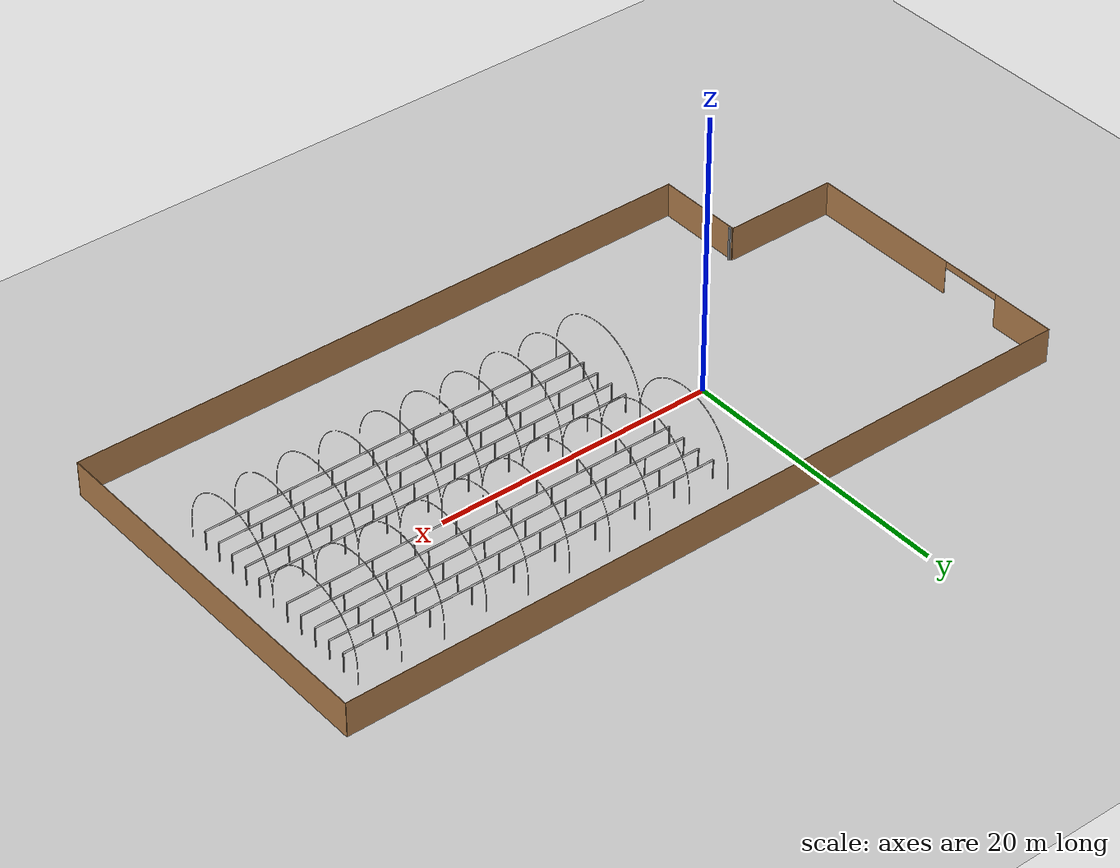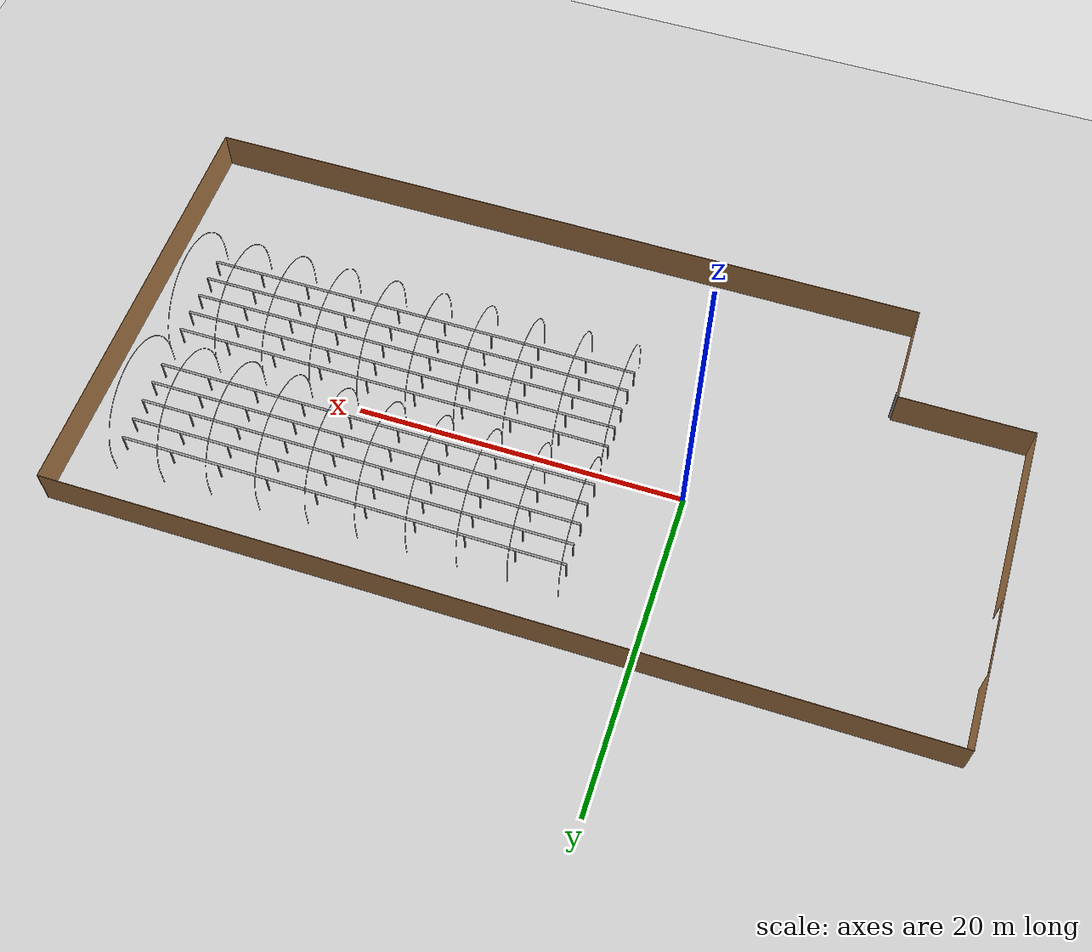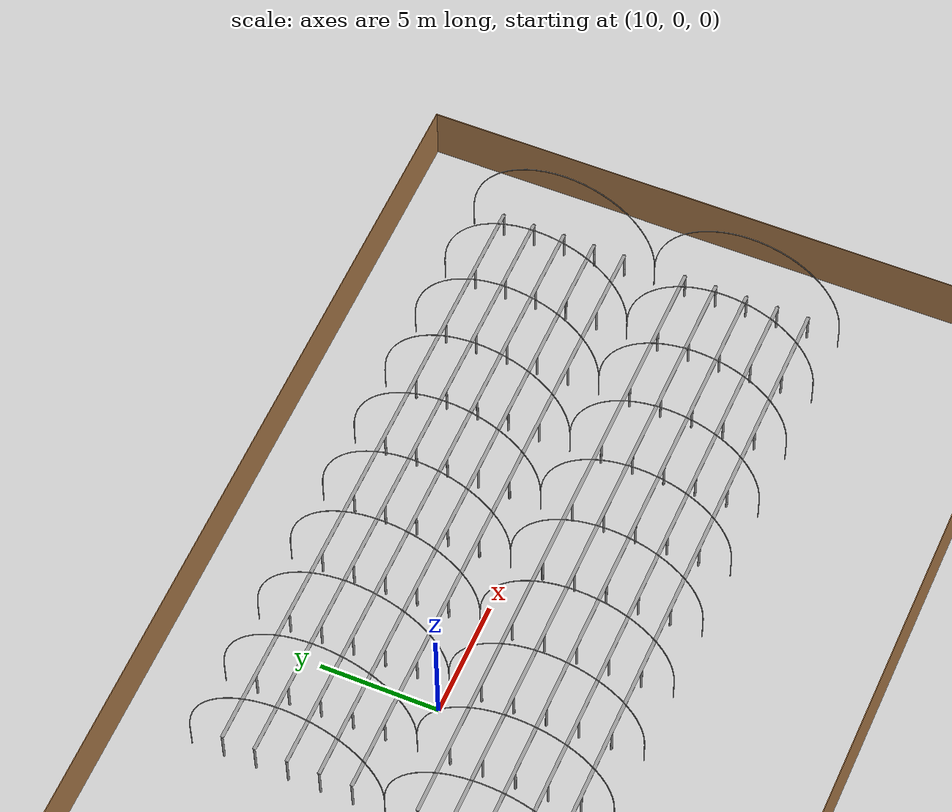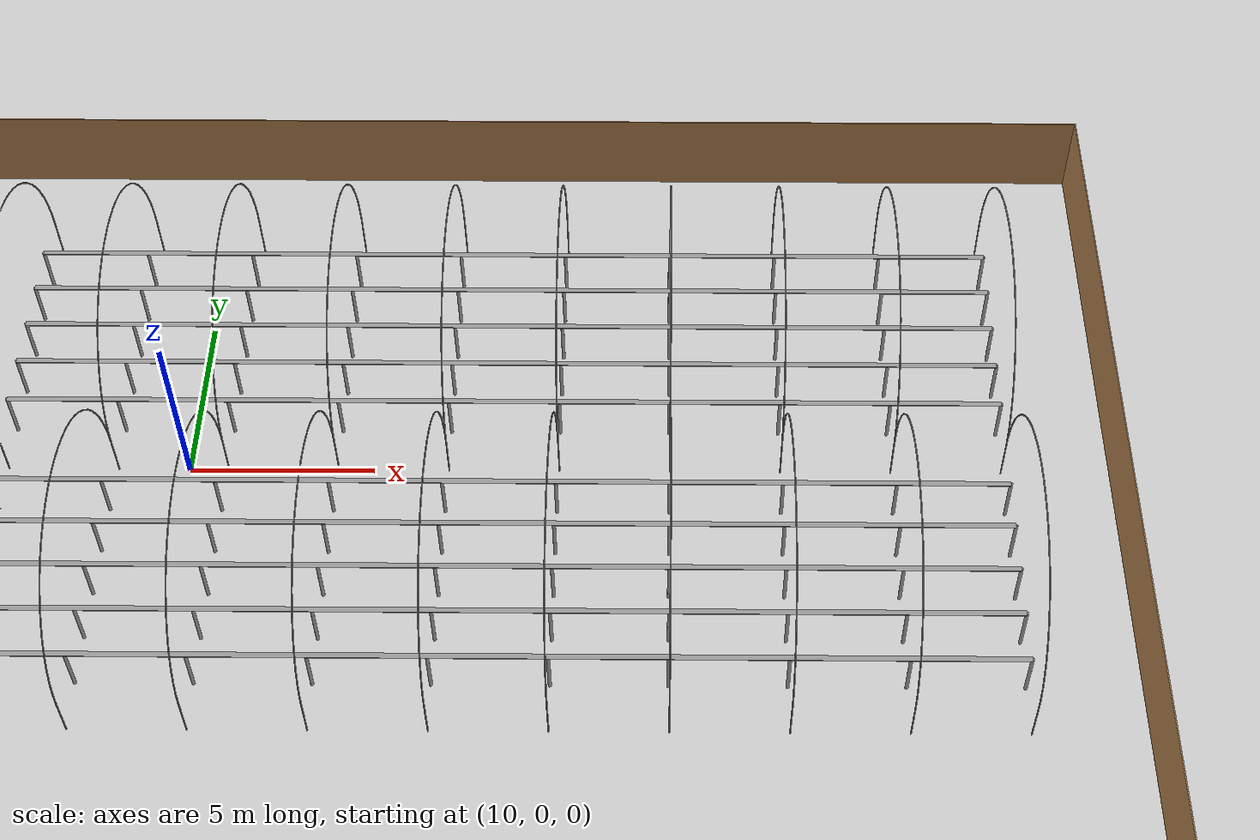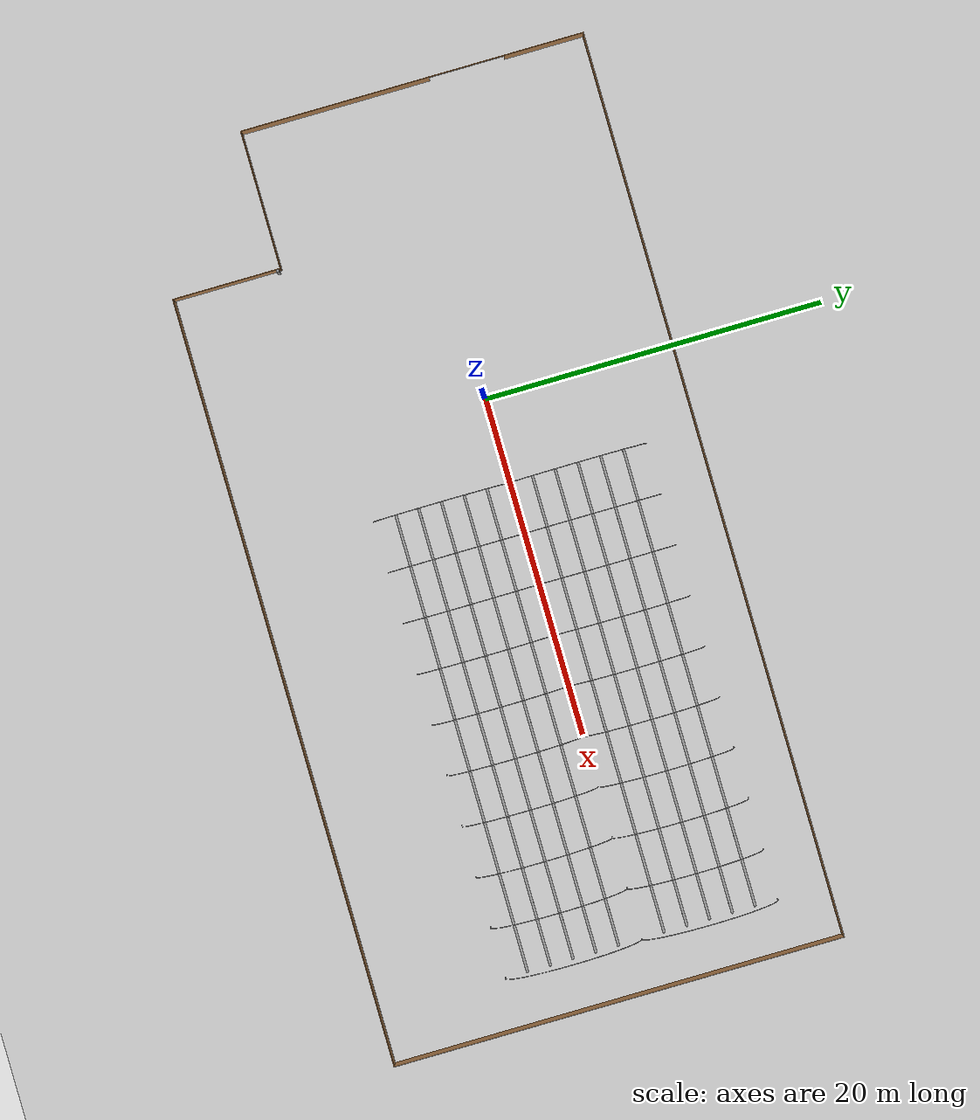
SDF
<sdf version="1.6">
 <world name="default">
  <model name="unit_cylinder_0">
   <static>1</static>
   <pose>5 1.35 0.691175 0 -0 0</pose>
   <link name="link">
    <inertial>
     <mass>1</mass>
     <inertia><ixz>0</ixz><ixx>1</ixx><ixy>0</ixy><izz>1</izz><iyy>1</iyy><iyz>0</iyz></inertia>
    </inertial>
    <collision name="collision">
     <geometry><cylinder><length>1.38235</length><radius>0.0456111</radius></cylinder></geometry>
    </collision>
    <visual name="visual">
     <geometry><cylinder><length>1.38235</length><radius>0.0456111</radius></cylinder></geometry>
     <material>
      <script><uri>file://media/materials/scripts/gazebo.material</uri><name>Gazebo/Grey</name></script>
     </material>
    </visual>
    <velocity_decay><linear>0</linear><angular>0</angular></velocity_decay>
   </link>
  </model>
  <model name="unit_cylinder_1">
   <static>1</static>
   <pose>5 2.7 0.691175 0 -0 0</pose>
   <link name="link">
    <inertial>
     <mass>1</mass>
     <inertia><ixz>0</ixz><ixx>1</ixx><ixy>0</ixy><izz>1</izz><iyy>1</iyy><iyz>0</iyz></inertia>
    </inertial>
    <collision name="collision">
     <geometry><cylinder><length>1.38235</length><radius>0.0456111</radius></cylinder></geometry>
    </collision>
    <visual name="visual">
     <geometry><cylinder><length>1.38235</length><radius>0.0456111</radius></cylinder></geometry>
     <material>
      <script><uri>file://media/materials/scripts/gazebo.material</uri><name>Gazebo/Grey</name></script>
     </material>
    </visual>
    <velocity_decay><linear>0</linear><angular>0</angular></velocity_decay>
   </link>
  </model>
  <model name="unit_cylinder_2">
   <static>1</static>
   <pose>5 4.05 0.691175 0 -0 0</pose>
   <link name="link">
    <inertial>
     <mass>1</mass>
     <inertia><ixz>0</ixz><ixx>1</ixx><ixy>0</ixy><izz>1</izz><iyy>1</iyy><iyz>0</iyz></inertia>
    </inertial>
    <collision name="collision">
     <geometry><cylinder><length>1.38235</length><radius>0.0456111</radius></cylinder></geometry>
    </collision>
    <visual name="visual">
     <geometry><cylinder><length>1.38235</length><radius>0.0456111</radius></cylinder></geometry>
     <material>
      <script><uri>file://media/materials/scripts/gazebo.material</uri><name>Gazebo/Grey</name></script>
     </material>
    </visual>
    <velocity_decay><linear>0</linear><angular>0</angular></velocity_decay>
   </link>
  </model>
  <model name="unit_cylinder_3">
   <static>1</static>
   <pose>5 5.4 0.691175 0 -0 0</pose>
   <link name="link">
    <inertial>
     <mass>1</mass>
     <inertia><ixz>0</ixz><ixx>1</ixx><ixy>0</ixy><izz>1</izz><iyy>1</iyy><iyz>0</iyz></inertia>
    </inertial>
    <collision name="collision">
     <geometry><cylinder><length>1.38235</length><radius>0.0456111</radius></cylinder></geometry>
    </collision>
    <visual name="visual">
     <geometry><cylinder><length>1.38235</length><radius>0.0456111</radius></cylinder></geometry>
     <material>
      <script><uri>file://media/materials/scripts/gazebo.material</uri><name>Gazebo/Grey</name></script>
     </material>
    </visual>
    <velocity_decay><linear>0</linear><angular>0</angular></velocity_decay>
   </link>
  </model>
  <model name="unit_cylinder_4">
   <static>1</static>
   <pose>5 6.75 0.691175 0 -0 0</pose>
   <link name="link">
    <inertial>
     <mass>1</mass>
     <inertia><ixz>0</ixz><ixx>1</ixx><ixy>0</ixy><izz>1</izz><iyy>1</iyy><iyz>0</iyz></inertia>
    </inertial>
    <collision name="collision">
     <geometry><cylinder><length>1.38235</length><radius>0.0456111</radius></cylinder></geometry>
    </collision>
    <visual name="visual">
     <geometry><cylinder><length>1.38235</length><radius>0.0456111</radius></cylinder></geometry>
     <material>
      <script><uri>file://media/materials/scripts/gazebo.material</uri><name>Gazebo/Grey</name></script>
     </material>
    </visual>
    <velocity_decay><linear>0</linear><angular>0</angular></velocity_decay>
   </link>
  </model>
  <model name="unit_cylinder_5">
   <static>1</static>
   <pose>8.01 1.35 0.691175 0 -0 0</pose>
   <link name="link">
    <inertial>
     <mass>1</mass>
     <inertia><ixz>0</ixz><ixx>1</ixx><ixy>0</ixy><izz>1</izz><iyy>1</iyy><iyz>0</iyz></inertia>
    </inertial>
    <collision name="collision">
     <geometry><cylinder><length>1.38235</length><radius>0.0456111</radius></cylinder></geometry>
    </collision>
    <visual name="visual">
     <geometry><cylinder><length>1.38235</length><radius>0.0456111</radius></cylinder></geometry>
     <material>
      <script><uri>file://media/materials/scripts/gazebo.material</uri><name>Gazebo/Grey</name></script>
     </material>
    </visual>
    <velocity_decay><linear>0</linear><angular>0</angular></velocity_decay>
   </link>
  </model>
  <model name="unit_cylinder_6">
   <static>1</static>
   <pose>8.01 2.7 0.691175 0 -0 0</pose>
   <link name="link">
    <inertial>
     <mass>1</mass>
     <inertia><ixz>0</ixz><ixx>1</ixx><ixy>0</ixy><izz>1</izz><iyy>1</iyy><iyz>0</iyz></inertia>
    </inertial>
    <collision name="collision">
     <geometry><cylinder><length>1.38235</length><radius>0.0456111</radius></cylinder></geometry>
    </collision>
    <visual name="visual">
     <geometry><cylinder><length>1.38235</length><radius>0.0456111</radius></cylinder></geometry>
     <material>
      <script><uri>file://media/materials/scripts/gazebo.material</uri><name>Gazebo/Grey</name></script>
     </material>
    </visual>
    <velocity_decay><linear>0</linear><angular>0</angular></velocity_decay>
   </link>
  </model>
  <model name="unit_cylinder_7">
   <static>1</static>
   <pose>8.01 4.05 0.691175 0 -0 0</pose>
   <link name="link">
    <inertial>
     <mass>1</mass>
     <inertia><ixz>0</ixz><ixx>1</ixx><ixy>0</ixy><izz>1</izz><iyy>1</iyy><iyz>0</iyz></inertia>
    </inertial>
    <collision name="collision">
     <geometry><cylinder><length>1.38235</length><radius>0.0456111</radius></cylinder></geometry>
    </collision>
    <visual name="visual">
     <geometry><cylinder><length>1.38235</length><radius>0.0456111</radius></cylinder></geometry>
     <material>
      <script><uri>file://media/materials/scripts/gazebo.material</uri><name>Gazebo/Grey</name></script>
     </material>
    </visual>
    <velocity_decay><linear>0</linear><angular>0</angular></velocity_decay>
   </link>
  </model>
  <model name="unit_cylinder_8">
   <static>1</static>
   <pose>8.01 5.4 0.691175 0 -0 0</pose>
   <link name="link">
    <inertial>
     <mass>1</mass>
     <inertia><ixz>0</ixz><ixx>1</ixx><ixy>0</ixy><izz>1</izz><iyy>1</iyy><iyz>0</iyz></inertia>
    </inertial>
    <collision name="collision">
     <geometry><cylinder><length>1.38235</length><radius>0.0456111</radius></cylinder></geometry>
    </collision>
    <visual name="visual">
     <geometry><cylinder><length>1.38235</length><radius>0.0456111</radius></cylinder></geometry>
     <material>
      <script><uri>file://media/materials/scripts/gazebo.material</uri><name>Gazebo/Grey</name></script>
     </material>
    </visual>
    <velocity_decay><linear>0</linear><angular>0</angular></velocity_decay>
   </link>
  </model>
  <model name="unit_cylinder_9">
   <static>1</static>
   <pose>8.01 6.75 0.691175 0 -0 0</pose>
   <link name="link">
    <inertial>
     <mass>1</mass>
     <inertia><ixz>0</ixz><ixx>1</ixx><ixy>0</ixy><izz>1</izz><iyy>1</iyy><iyz>0</iyz></inertia>
    </inertial>
    <collision name="collision">
     <geometry><cylinder><length>1.38235</length><radius>0.0456111</radius></cylinder></geometry>
    </collision>
    <visual name="visual">
     <geometry><cylinder><length>1.38235</length><radius>0.0456111</radius></cylinder></geometry>
     <material>
      <script><uri>file://media/materials/scripts/gazebo.material</uri><name>Gazebo/Grey</name></script>
     </material>
    </visual>
    <velocity_decay><linear>0</linear><angular>0</angular></velocity_decay>
   </link>
  </model>
  <model name="unit_cylinder_10">
   <static>1</static>
   <pose>11.02 1.35 0.691175 0 -0 0</pose>
   <link name="link">
    <inertial>
     <mass>1</mass>
     <inertia><ixz>0</ixz><ixx>1</ixx><ixy>0</ixy><izz>1</izz><iyy>1</iyy><iyz>0</iyz></inertia>
    </inertial>
    <collision name="collision">
     <geometry><cylinder><length>1.38235</length><radius>0.0456111</radius></cylinder></geometry>
    </collision>
    <visual name="visual">
     <geometry><cylinder><length>1.38235</length><radius>0.0456111</radius></cylinder></geometry>
     <material>
      <script><uri>file://media/materials/scripts/gazebo.material</uri><name>Gazebo/Grey</name></script>
     </material>
    </visual>
    <velocity_decay><linear>0</linear><angular>0</angular></velocity_decay>
   </link>
  </model>
  <model name="unit_cylinder_11">
   <static>1</static>
   <pose>11.02 2.7 0.691175 0 -0 0</pose>
   <link name="link">
    <inertial>
     <mass>1</mass>
     <inertia><ixz>0</ixz><ixx>1</ixx><ixy>0</ixy><izz>1</izz><iyy>1</iyy><iyz>0</iyz></inertia>
    </inertial>
    <collision name="collision">
     <geometry><cylinder><length>1.38235</length><radius>0.0456111</radius></cylinder></geometry>
    </collision>
    <visual name="visual">
     <geometry><cylinder><length>1.38235</length><radius>0.0456111</radius></cylinder></geometry>
     <material>
      <script><uri>file://media/materials/scripts/gazebo.material</uri><name>Gazebo/Grey</name></script>
     </material>
    </visual>
    <velocity_decay><linear>0</linear><angular>0</angular></velocity_decay>
   </link>
  </model>
  <model name="unit_cylinder_12">
   <static>1</static>
   <pose>11.02 4.05 0.691175 0 -0 0</pose>
   <link name="link">
    <inertial>
     <mass>1</mass>
     <inertia><ixz>0</ixz><ixx>1</ixx><ixy>0</ixy><izz>1</izz><iyy>1</iyy><iyz>0</iyz></inertia>
    </inertial>
    <collision name="collision">
     <geometry><cylinder><length>1.38235</length><radius>0.0456111</radius></cylinder></geometry>
    </collision>
    <visual name="visual">
     <geometry><cylinder><length>1.38235</length><radius>0.0456111</radius></cylinder></geometry>
     <material>
      <script><uri>file://media/materials/scripts/gazebo.material</uri><name>Gazebo/Grey</name></script>
     </material>
    </visual>
    <velocity_decay><linear>0</linear><angular>0</angular></velocity_decay>
   </link>
  </model>
  <model name="unit_cylinder_13">
   <static>1</static>
   <pose>11.02 5.4 0.691175 0 -0 0</pose>
   <link name="link">
    <inertial>
     <mass>1</mass>
     <inertia><ixz>0</ixz><ixx>1</ixx><ixy>0</ixy><izz>1</izz><iyy>1</iyy><iyz>0</iyz></inertia>
    </inertial>
    <collision name="collision">
     <geometry><cylinder><length>1.38235</length><radius>0.0456111</radius></cylinder></geometry>
    </collision>
    <visual name="visual">
     <geometry><cylinder><length>1.38235</length><radius>0.0456111</radius></cylinder></geometry>
     <material>
      <script><uri>file://media/materials/scripts/gazebo.material</uri><name>Gazebo/Grey</name></script>
     </material>
    </visual>
    <velocity_decay><linear>0</linear><angular>0</angular></velocity_decay>
   </link>
  </model>
  <model name="unit_cylinder_14">
   <static>1</static>
   <pose>11.02 6.75 0.691175 0 -0 0</pose>
   <link name="link">
    <inertial>
     <mass>1</mass>
     <inertia><ixz>0</ixz><ixx>1</ixx><ixy>0</ixy><izz>1</izz><iyy>1</iyy><iyz>0</iyz></inertia>
    </inertial>
    <collision name="collision">
     <geometry><cylinder><length>1.38235</length><radius>0.0456111</radius></cylinder></geometry>
    </collision>
    <visual name="visual">
     <geometry><cylinder><length>1.38235</length><radius>0.0456111</radius></cylinder></geometry>
     <material>
      <script><uri>file://media/materials/scripts/gazebo.material</uri><name>Gazebo/Grey</name></script>
     </material>
    </visual>
    <velocity_decay><linear>0</linear><angular>0</angular></velocity_decay>
   </link>
  </model>
  <model name="unit_cylinder_15">
   <static>1</static>
   <pose>14.03 1.35 0.691175 0 -0 0</pose>
   <link name="link">
    <inertial>
     <mass>1</mass>
     <inertia><ixz>0</ixz><ixx>1</ixx><ixy>0</ixy><izz>1</izz><iyy>1</iyy><iyz>0</iyz></inertia>
    </inertial>
    <collision name="collision">
     <geometry><cylinder><length>1.38235</length><radius>0.0456111</radius></cylinder></geometry>
    </collision>
    <visual name="visual">
     <geometry><cylinder><length>1.38235</length><radius>0.0456111</radius></cylinder></geometry>
     <material>
      <script><uri>file://media/materials/scripts/gazebo.material</uri><name>Gazebo/Grey</name></script>
     </material>
    </visual>
    <velocity_decay><linear>0</linear><angular>0</angular></velocity_decay>
   </link>
  </model>
  <model name="unit_cylinder_16">
   <static>1</static>
   <pose>14.03 2.7 0.691175 0 -0 0</pose>
   <link name="link">
    <inertial>
     <mass>1</mass>
     <inertia><ixz>0</ixz><ixx>1</ixx><ixy>0</ixy><izz>1</izz><iyy>1</iyy><iyz>0</iyz></inertia>
    </inertial>
    <collision name="collision">
     <geometry><cylinder><length>1.38235</length><radius>0.0456111</radius></cylinder></geometry>
    </collision>
    <visual name="visual">
     <geometry><cylinder><length>1.38235</length><radius>0.0456111</radius></cylinder></geometry>
     <material>
      <script><uri>file://media/materials/scripts/gazebo.material</uri><name>Gazebo/Grey</name></script>
     </material>
    </visual>
    <velocity_decay><linear>0</linear><angular>0</angular></velocity_decay>
   </link>
  </model>
  <model name="unit_cylinder_17">
   <static>1</static>
   <pose>14.03 4.05 0.691175 0 -0 0</pose>
   <link name="link">
    <inertial>
     <mass>1</mass>
     <inertia><ixz>0</ixz><ixx>1</ixx><ixy>0</ixy><izz>1</izz><iyy>1</iyy><iyz>0</iyz></inertia>
    </inertial>
    <collision name="collision">
     <geometry><cylinder><length>1.38235</length><radius>0.0456111</radius></cylinder></geometry>
    </collision>
    <visual name="visual">
     <geometry><cylinder><length>1.38235</length><radius>0.0456111</radius></cylinder></geometry>
     <material>
      <script><uri>file://media/materials/scripts/gazebo.material</uri><name>Gazebo/Grey</name></script>
     </material>
    </visual>
    <velocity_decay><linear>0</linear><angular>0</angular></velocity_decay>
   </link>
  </model>
  <model name="unit_cylinder_18">
   <static>1</static>
   <pose>14.03 5.4 0.691175 0 -0 0</pose>
   <link name="link">
    <inertial>
     <mass>1</mass>
     <inertia><ixz>0</ixz><ixx>1</ixx><ixy>0</ixy><izz>1</izz><iyy>1</iyy><iyz>0</iyz></inertia>
    </inertial>
    <collision name="collision">
     <geometry><cylinder><length>1.38235</length><radius>0.0456111</radius></cylinder></geometry>
    </collision>
    <visual name="visual">
     <geometry><cylinder><length>1.38235</length><radius>0.0456111</radius></cylinder></geometry>
     <material>
      <script><uri>file://media/materials/scripts/gazebo.material</uri><name>Gazebo/Grey</name></script>
     </material>
    </visual>
    <velocity_decay><linear>0</linear><angular>0</angular></velocity_decay>
   </link>
  </model>
  <model name="unit_cylinder_19">
   <static>1</static>
   <pose>14.03 6.75 0.691175 0 -0 0</pose>
   <link name="link">
    <inertial>
     <mass>1</mass>
     <inertia><ixz>0</ixz><ixx>1</ixx><ixy>0</ixy><izz>1</izz><iyy>1</iyy><iyz>0</iyz></inertia>
    </inertial>
    <collision name="collision">
     <geometry><cylinder><length>1.38235</length><radius>0.0456111</radius></cylinder></geometry>
    </collision>
    <visual name="visual">
     <geometry><cylinder><length>1.38235</length><radius>0.0456111</radius></cylinder></geometry>
     <material>
      <script><uri>file://media/materials/scripts/gazebo.material</uri><name>Gazebo/Grey</name></script>
     </material>
    </visual>
    <velocity_decay><linear>0</linear><angular>0</angular></velocity_decay>
   </link>
  </model>
  <model name="unit_cylinder_20">
   <static>1</static>
   <pose>17.04 1.35 0.691175 0 -0 0</pose>
   <link name="link">
    <inertial>
     <mass>1</mass>
     <inertia><ixz>0</ixz><ixx>1</ixx><ixy>0</ixy><izz>1</izz><iyy>1</iyy><iyz>0</iyz></inertia>
    </inertial>
    <collision name="collision">
     <geometry><cylinder><length>1.38235</length><radius>0.0456111</radius></cylinder></geometry>
    </collision>
    <visual name="visual">
     <geometry><cylinder><length>1.38235</length><radius>0.0456111</radius></cylinder></geometry>
     <material>
      <script><uri>file://media/materials/scripts/gazebo.material</uri><name>Gazebo/Grey</name></script>
     </material>
    </visual>
    <velocity_decay><linear>0</linear><angular>0</angular></velocity_decay>
   </link>
  </model>
  <model name="unit_cylinder_21">
   <static>1</static>
   <pose>17.04 2.7 0.691175 0 -0 0</pose>
   <link name="link">
    <inertial>
     <mass>1</mass>
     <inertia><ixz>0</ixz><ixx>1</ixx><ixy>0</ixy><izz>1</izz><iyy>1</iyy><iyz>0</iyz></inertia>
    </inertial>
    <collision name="collision">
     <geometry><cylinder><length>1.38235</length><radius>0.0456111</radius></cylinder></geometry>
    </collision>
    <visual name="visual">
     <geometry><cylinder><length>1.38235</length><radius>0.0456111</radius></cylinder></geometry>
     <material>
      <script><uri>file://media/materials/scripts/gazebo.material</uri><name>Gazebo/Grey</name></script>
     </material>
    </visual>
    <velocity_decay><linear>0</linear><angular>0</angular></velocity_decay>
   </link>
  </model>
  <model name="unit_cylinder_22">
   <static>1</static>
   <pose>17.04 4.05 0.691175 0 -0 0</pose>
   <link name="link">
    <inertial>
     <mass>1</mass>
     <inertia><ixz>0</ixz><ixx>1</ixx><ixy>0</ixy><izz>1</izz><iyy>1</iyy><iyz>0</iyz></inertia>
    </inertial>
    <collision name="collision">
     <geometry><cylinder><length>1.38235</length><radius>0.0456111</radius></cylinder></geometry>
    </collision>
    <visual name="visual">
     <geometry><cylinder><length>1.38235</length><radius>0.0456111</radius></cylinder></geometry>
     <material>
      <script><uri>file://media/materials/scripts/gazebo.material</uri><name>Gazebo/Grey</name></script>
     </material>
    </visual>
    <velocity_decay><linear>0</linear><angular>0</angular></velocity_decay>
   </link>
  </model>
  <model name="unit_cylinder_23">
   <static>1</static>
   <pose>17.04 5.4 0.691175 0 -0 0</pose>
   <link name="link">
    <inertial>
     <mass>1</mass>
     <inertia><ixz>0</ixz><ixx>1</ixx><ixy>0</ixy><izz>1</izz><iyy>1</iyy><iyz>0</iyz></inertia>
    </inertial>
    <collision name="collision">
     <geometry><cylinder><length>1.38235</length><radius>0.0456111</radius></cylinder></geometry>
    </collision>
    <visual name="visual">
     <geometry><cylinder><length>1.38235</length><radius>0.0456111</radius></cylinder></geometry>
     <material>
      <script><uri>file://media/materials/scripts/gazebo.material</uri><name>Gazebo/Grey</name></script>
     </material>
    </visual>
    <velocity_decay><linear>0</linear><angular>0</angular></velocity_decay>
   </link>
  </model>
  <model name="unit_cylinder_24">
   <static>1</static>
   <pose>17.04 6.75 0.691175 0 -0 0</pose>
   <link name="link">
    <inertial>
     <mass>1</mass>
     <inertia><ixz>0</ixz><ixx>1</ixx><ixy>0</ixy><izz>1</izz><iyy>1</iyy><iyz>0</iyz></inertia>
    </inertial>
    <collision name="collision">
     <geometry><cylinder><length>1.38235</length><radius>0.0456111</radius></cylinder></geometry>
    </collision>
    <visual name="visual">
     <geometry><cylinder><length>1.38235</length><radius>0.0456111</radius></cylinder></geometry>
     <material>
      <script><uri>file://media/materials/scripts/gazebo.material</uri><name>Gazebo/Grey</name></script>
     </material>
    </visual>
    <velocity_decay><linear>0</linear><angular>0</angular></velocity_decay>
   </link>
  </model>
  <model name="unit_cylinder_25">
   <static>1</static>
   <pose>20.05 1.35 0.691175 0 -0 0</pose>
   <link name="link">
    <inertial>
     <mass>1</mass>
     <inertia><ixz>0</ixz><ixx>1</ixx><ixy>0</ixy><izz>1</izz><iyy>1</iyy><iyz>0</iyz></inertia>
    </inertial>
    <collision name="collision">
     <geometry><cylinder><length>1.38235</length><radius>0.0456111</radius></cylinder></geometry>
    </collision>
    <visual name="visual">
     <geometry><cylinder><length>1.38235</length><radius>0.0456111</radius></cylinder></geometry>
     <material>
      <script><uri>file://media/materials/scripts/gazebo.material</uri><name>Gazebo/Grey</name></script>
     </material>
    </visual>
    <velocity_decay><linear>0</linear><angular>0</angular></velocity_decay>
   </link>
  </model>
  <model name="unit_cylinder_26">
   <static>1</static>
   <pose>20.05 2.7 0.691175 0 -0 0</pose>
   <link name="link">
    <inertial>
     <mass>1</mass>
     <inertia><ixz>0</ixz><ixx>1</ixx><ixy>0</ixy><izz>1</izz><iyy>1</iyy><iyz>0</iyz></inertia>
    </inertial>
    <collision name="collision">
     <geometry><cylinder><length>1.38235</length><radius>0.0456111</radius></cylinder></geometry>
    </collision>
    <visual name="visual">
     <geometry><cylinder><length>1.38235</length><radius>0.0456111</radius></cylinder></geometry>
     <material>
      <script><uri>file://media/materials/scripts/gazebo.material</uri><name>Gazebo/Grey</name></script>
     </material>
    </visual>
    <velocity_decay><linear>0</linear><angular>0</angular></velocity_decay>
   </link>
  </model>
  <model name="unit_cylinder_27">
   <static>1</static>
   <pose>20.05 4.05 0.691175 0 -0 0</pose>
   <link name="link">
    <inertial>
     <mass>1</mass>
     <inertia><ixz>0</ixz><ixx>1</ixx><ixy>0</ixy><izz>1</izz><iyy>1</iyy><iyz>0</iyz></inertia>
    </inertial>
    <collision name="collision">
     <geometry><cylinder><length>1.38235</length><radius>0.0456111</radius></cylinder></geometry>
    </collision>
    <visual name="visual">
     <geometry><cylinder><length>1.38235</length><radius>0.0456111</radius></cylinder></geometry>
     <material>
      <script><uri>file://media/materials/scripts/gazebo.material</uri><name>Gazebo/Grey</name></script>
     </material>
    </visual>
    <velocity_decay><linear>0</linear><angular>0</angular></velocity_decay>
   </link>
  </model>
  <model name="unit_cylinder_28">
   <static>1</static>
   <pose>20.05 5.4 0.691175 0 -0 0</pose>
   <link name="link">
    <inertial>
     <mass>1</mass>
     <inertia><ixz>0</ixz><ixx>1</ixx><ixy>0</ixy><izz>1</izz><iyy>1</iyy><iyz>0</iyz></inertia>
    </inertial>
    <collision name="collision">
     <geometry><cylinder><length>1.38235</length><radius>0.0456111</radius></cylinder></geometry>
    </collision>
    <visual name="visual">
     <geometry><cylinder><length>1.38235</length><radius>0.0456111</radius></cylinder></geometry>
     <material>
      <script><uri>file://media/materials/scripts/gazebo.material</uri><name>Gazebo/Grey</name></script>
     </material>
    </visual>
    <velocity_decay><linear>0</linear><angular>0</angular></velocity_decay>
   </link>
  </model>
  <model name="unit_cylinder_29">
   <static>1</static>
   <pose>20.05 6.75 0.691175 0 -0 0</pose>
   <link name="link">
    <inertial>
     <mass>1</mass>
     <inertia><ixz>0</ixz><ixx>1</ixx><ixy>0</ixy><izz>1</izz><iyy>1</iyy><iyz>0</iyz></inertia>
    </inertial>
    <collision name="collision">
     <geometry><cylinder><length>1.38235</length><radius>0.0456111</radius></cylinder></geometry>
    </collision>
    <visual name="visual">
     <geometry><cylinder><length>1.38235</length><radius>0.0456111</radius></cylinder></geometry>
     <material>
      <script><uri>file://media/materials/scripts/gazebo.material</uri><name>Gazebo/Grey</name></script>
     </material>
    </visual>
    <velocity_decay><linear>0</linear><angular>0</angular></velocity_decay>
   </link>
  </model>
  <model name="unit_cylinder_30">
   <static>1</static>
   <pose>23.06 1.35 0.691175 0 -0 0</pose>
   <link name="link">
    <inertial>
     <mass>1</mass>
     <inertia><ixz>0</ixz><ixx>1</ixx><ixy>0</ixy><izz>1</izz><iyy>1</iyy><iyz>0</iyz></inertia>
    </inertial>
    <collision name="collision">
     <geometry><cylinder><length>1.38235</length><radius>0.0456111</radius></cylinder></geometry>
    </collision>
    <visual name="visual">
     <geometry><cylinder><length>1.38235</length><radius>0.0456111</radius></cylinder></geometry>
     <material>
      <script><uri>file://media/materials/scripts/gazebo.material</uri><name>Gazebo/Grey</name></script>
     </material>
    </visual>
    <velocity_decay><linear>0</linear><angular>0</angular></velocity_decay>
   </link>
  </model>
  <model name="unit_cylinder_31">
   <static>1</static>
   <pose>23.06 2.7 0.691175 0 -0 0</pose>
   <link name="link">
    <inertial>
     <mass>1</mass>
     <inertia><ixz>0</ixz><ixx>1</ixx><ixy>0</ixy><izz>1</izz><iyy>1</iyy><iyz>0</iyz></inertia>
    </inertial>
    <collision name="collision">
     <geometry><cylinder><length>1.38235</length><radius>0.0456111</radius></cylinder></geometry>
    </collision>
    <visual name="visual">
     <geometry><cylinder><length>1.38235</length><radius>0.0456111</radius></cylinder></geometry>
     <material>
      <script><uri>file://media/materials/scripts/gazebo.material</uri><name>Gazebo/Grey</name></script>
     </material>
    </visual>
    <velocity_decay><linear>0</linear><angular>0</angular></velocity_decay>
   </link>
  </model>
  <model name="unit_cylinder_32">
   <static>1</static>
   <pose>23.06 4.05 0.691175 0 -0 0</pose>
   <link name="link">
    <inertial>
     <mass>1</mass>
     <inertia><ixz>0</ixz><ixx>1</ixx><ixy>0</ixy><izz>1</izz><iyy>1</iyy><iyz>0</iyz></inertia>
    </inertial>
    <collision name="collision">
     <geometry><cylinder><length>1.38235</length><radius>0.0456111</radius></cylinder></geometry>
    </collision>
    <visual name="visual">
     <geometry><cylinder><length>1.38235</length><radius>0.0456111</radius></cylinder></geometry>
     <material>
      <script><uri>file://media/materials/scripts/gazebo.material</uri><name>Gazebo/Grey</name></script>
     </material>
    </visual>
    <velocity_decay><linear>0</linear><angular>0</angular></velocity_decay>
   </link>
  </model>
  <model name="unit_cylinder_33">
   <static>1</static>
   <pose>23.06 5.4 0.691175 0 -0 0</pose>
   <link name="link">
    <inertial>
     <mass>1</mass>
     <inertia><ixz>0</ixz><ixx>1</ixx><ixy>0</ixy><izz>1</izz><iyy>1</iyy><iyz>0</iyz></inertia>
    </inertial>
    <collision name="collision">
     <geometry><cylinder><length>1.38235</length><radius>0.0456111</radius></cylinder></geometry>
    </collision>
    <visual name="visual">
     <geometry><cylinder><length>1.38235</length><radius>0.0456111</radius></cylinder></geometry>
     <material>
      <script><uri>file://media/materials/scripts/gazebo.material</uri><name>Gazebo/Grey</name></script>
     </material>
    </visual>
    <velocity_decay><linear>0</linear><angular>0</angular></velocity_decay>
   </link>
  </model>
  <model name="unit_cylinder_34">
   <static>1</static>
   <pose>23.06 6.75 0.691175 0 -0 0</pose>
   <link name="link">
    <inertial>
     <mass>1</mass>
     <inertia><ixz>0</ixz><ixx>1</ixx><ixy>0</ixy><izz>1</izz><iyy>1</iyy><iyz>0</iyz></inertia>
    </inertial>
    <collision name="collision">
     <geometry><cylinder><length>1.38235</length><radius>0.0456111</radius></cylinder></geometry>
    </collision>
    <visual name="visual">
     <geometry><cylinder><length>1.38235</length><radius>0.0456111</radius></cylinder></geometry>
     <material>
      <script><uri>file://media/materials/scripts/gazebo.material</uri><name>Gazebo/Grey</name></script>
     </material>
    </visual>
    <velocity_decay><linear>0</linear><angular>0</angular></velocity_decay>
   </link>
  </model>
  <model name="unit_cylinder_35">
   <static>1</static>
   <pose>26.07 1.35 0.691175 0 -0 0</pose>
   <link name="link">
    <inertial>
     <mass>1</mass>
     <inertia><ixz>0</ixz><ixx>1</ixx><ixy>0</ixy><izz>1</izz><iyy>1</iyy><iyz>0</iyz></inertia>
    </inertial>
    <collision name="collision">
     <geometry><cylinder><length>1.38235</length><radius>0.0456111</radius></cylinder></geometry>
    </collision>
    <visual name="visual">
     <geometry><cylinder><length>1.38235</length><radius>0.0456111</radius></cylinder></geometry>
     <material>
      <script><uri>file://media/materials/scripts/gazebo.material</uri><name>Gazebo/Grey</name></script>
     </material>
    </visual>
    <velocity_decay><linear>0</linear><angular>0</angular></velocity_decay>
   </link>
  </model>
  <model name="unit_cylinder_36">
   <static>1</static>
   <pose>26.07 2.7 0.691175 0 -0 0</pose>
   <link name="link">
    <inertial>
     <mass>1</mass>
     <inertia><ixz>0</ixz><ixx>1</ixx><ixy>0</ixy><izz>1</izz><iyy>1</iyy><iyz>0</iyz></inertia>
    </inertial>
    <collision name="collision">
     <geometry><cylinder><length>1.38235</length><radius>0.0456111</radius></cylinder></geometry>
    </collision>
    <visual name="visual">
     <geometry><cylinder><length>1.38235</length><radius>0.0456111</radius></cylinder></geometry>
     <material>
      <script><uri>file://media/materials/scripts/gazebo.material</uri><name>Gazebo/Grey</name></script>
     </material>
    </visual>
    <velocity_decay><linear>0</linear><angular>0</angular></velocity_decay>
   </link>
  </model>
  <model name="unit_cylinder_37">
   <static>1</static>
   <pose>26.07 4.05 0.691175 0 -0 0</pose>
   <link name="link">
    <inertial>
     <mass>1</mass>
     <inertia><ixz>0</ixz><ixx>1</ixx><ixy>0</ixy><izz>1</izz><iyy>1</iyy><iyz>0</iyz></inertia>
    </inertial>
    <collision name="collision">
     <geometry><cylinder><length>1.38235</length><radius>0.0456111</radius></cylinder></geometry>
    </collision>
    <visual name="visual">
     <geometry><cylinder><length>1.38235</length><radius>0.0456111</radius></cylinder></geometry>
     <material>
      <script><uri>file://media/materials/scripts/gazebo.material</uri><name>Gazebo/Grey</name></script>
     </material>
    </visual>
    <velocity_decay><linear>0</linear><angular>0</angular></velocity_decay>
   </link>
  </model>
  <model name="unit_cylinder_38">
   <static>1</static>
   <pose>26.07 5.4 0.691175 0 -0 0</pose>
   <link name="link">
    <inertial>
     <mass>1</mass>
     <inertia><ixz>0</ixz><ixx>1</ixx><ixy>0</ixy><izz>1</izz><iyy>1</iyy><iyz>0</iyz></inertia>
    </inertial>
    <collision name="collision">
     <geometry><cylinder><length>1.38235</length><radius>0.0456111</radius></cylinder></geometry>
    </collision>
    <visual name="visual">
     <geometry><cylinder><length>1.38235</length><radius>0.0456111</radius></cylinder></geometry>
     <material>
      <script><uri>file://media/materials/scripts/gazebo.material</uri><name>Gazebo/Grey</name></script>
     </material>
    </visual>
    <velocity_decay><linear>0</linear><angular>0</angular></velocity_decay>
   </link>
  </model>
  <model name="unit_cylinder_39">
   <static>1</static>
   <pose>26.07 6.75 0.691175 0 -0 0</pose>
   <link name="link">
    <inertial>
     <mass>1</mass>
     <inertia><ixz>0</ixz><ixx>1</ixx><ixy>0</ixy><izz>1</izz><iyy>1</iyy><iyz>0</iyz></inertia>
    </inertial>
    <collision name="collision">
     <geometry><cylinder><length>1.38235</length><radius>0.0456111</radius></cylinder></geometry>
    </collision>
    <visual name="visual">
     <geometry><cylinder><length>1.38235</length><radius>0.0456111</radius></cylinder></geometry>
     <material>
      <script><uri>file://media/materials/scripts/gazebo.material</uri><name>Gazebo/Grey</name></script>
     </material>
    </visual>
    <velocity_decay><linear>0</linear><angular>0</angular></velocity_decay>
   </link>
  </model>
  <model name="unit_cylinder_40">
   <static>1</static>
   <pose>29.08 1.35 0.691175 0 -0 0</pose>
   <link name="link">
    <inertial>
     <mass>1</mass>
     <inertia><ixz>0</ixz><ixx>1</ixx><ixy>0</ixy><izz>1</izz><iyy>1</iyy><iyz>0</iyz></inertia>
    </inertial>
    <collision name="collision">
     <geometry><cylinder><length>1.38235</length><radius>0.0456111</radius></cylinder></geometry>
    </collision>
    <visual name="visual">
     <geometry><cylinder><length>1.38235</length><radius>0.0456111</radius></cylinder></geometry>
     <material>
      <script><uri>file://media/materials/scripts/gazebo.material</uri><name>Gazebo/Grey</name></script>
     </material>
    </visual>
    <velocity_decay><linear>0</linear><angular>0</angular></velocity_decay>
   </link>
  </model>
  <model name="unit_cylinder_41">
   <static>1</static>
   <pose>29.08 2.7 0.691175 0 -0 0</pose>
   <link name="link">
    <inertial>
     <mass>1</mass>
     <inertia><ixz>0</ixz><ixx>1</ixx><ixy>0</ixy><izz>1</izz><iyy>1</iyy><iyz>0</iyz></inertia>
    </inertial>
    <collision name="collision">
     <geometry><cylinder><length>1.38235</length><radius>0.0456111</radius></cylinder></geometry>
    </collision>
    <visual name="visual">
     <geometry><cylinder><length>1.38235</length><radius>0.0456111</radius></cylinder></geometry>
     <material>
      <script><uri>file://media/materials/scripts/gazebo.material</uri><name>Gazebo/Grey</name></script>
     </material>
    </visual>
    <velocity_decay><linear>0</linear><angular>0</angular></velocity_decay>
   </link>
  </model>
  <model name="unit_cylinder_42">
   <static>1</static>
   <pose>29.08 4.05 0.691175 0 -0 0</pose>
   <link name="link">
    <inertial>
     <mass>1</mass>
     <inertia><ixz>0</ixz><ixx>1</ixx><ixy>0</ixy><izz>1</izz><iyy>1</iyy><iyz>0</iyz></inertia>
    </inertial>
    <collision name="collision">
     <geometry><cylinder><length>1.38235</length><radius>0.0456111</radius></cylinder></geometry>
    </collision>
    <visual name="visual">
     <geometry><cylinder><length>1.38235</length><radius>0.0456111</radius></cylinder></geometry>
     <material>
      <script><uri>file://media/materials/scripts/gazebo.material</uri><name>Gazebo/Grey</name></script>
     </material>
    </visual>
    <velocity_decay><linear>0</linear><angular>0</angular></velocity_decay>
   </link>
  </model>
  <model name="unit_cylinder_43">
   <static>1</static>
   <pose>29.08 5.4 0.691175 0 -0 0</pose>
   <link name="link">
    <inertial>
     <mass>1</mass>
     <inertia><ixz>0</ixz><ixx>1</ixx><ixy>0</ixy><izz>1</izz><iyy>1</iyy><iyz>0</iyz></inertia>
    </inertial>
    <collision name="collision">
     <geometry><cylinder><length>1.38235</length><radius>0.0456111</radius></cylinder></geometry>
    </collision>
    <visual name="visual">
     <geometry><cylinder><length>1.38235</length><radius>0.0456111</radius></cylinder></geometry>
     <material>
      <script><uri>file://media/materials/scripts/gazebo.material</uri><name>Gazebo/Grey</name></script>
     </material>
    </visual>
    <velocity_decay><linear>0</linear><angular>0</angular></velocity_decay>
   </link>
  </model>
  <model name="unit_cylinder_44">
   <static>1</static>
   <pose>29.08 6.75 0.691175 0 -0 0</pose>
   <link name="link">
    <inertial>
     <mass>1</mass>
     <inertia><ixz>0</ixz><ixx>1</ixx><ixy>0</ixy><izz>1</izz><iyy>1</iyy><iyz>0</iyz></inertia>
    </inertial>
    <collision name="collision">
     <geometry><cylinder><length>1.38235</length><radius>0.0456111</radius></cylinder></geometry>
    </collision>
    <visual name="visual">
     <geometry><cylinder><length>1.38235</length><radius>0.0456111</radius></cylinder></geometry>
     <material>
      <script><uri>file://media/materials/scripts/gazebo.material</uri><name>Gazebo/Grey</name></script>
     </material>
    </visual>
    <velocity_decay><linear>0</linear><angular>0</angular></velocity_decay>
   </link>
  </model>
  <model name="unit_cylinder_45">
   <static>1</static>
   <pose>32.09 1.35 0.691175 0 -0 0</pose>
   <link name="link">
    <inertial>
     <mass>1</mass>
     <inertia><ixz>0</ixz><ixx>1</ixx><ixy>0</ixy><izz>1</izz><iyy>1</iyy><iyz>0</iyz></inertia>
    </inertial>
    <collision name="collision">
     <geometry><cylinder><length>1.38235</length><radius>0.0456111</radius></cylinder></geometry>
    </collision>
    <visual name="visual">
     <geometry><cylinder><length>1.38235</length><radius>0.0456111</radius></cylinder></geometry>
     <material>
      <script><uri>file://media/materials/scripts/gazebo.material</uri><name>Gazebo/Grey</name></script>
     </material>
    </visual>
    <velocity_decay><linear>0</linear><angular>0</angular></velocity_decay>
   </link>
  </model>
  <model name="unit_cylinder_46">
   <static>1</static>
   <pose>32.09 2.7 0.691175 0 -0 0</pose>
   <link name="link">
    <inertial>
     <mass>1</mass>
     <inertia><ixz>0</ixz><ixx>1</ixx><ixy>0</ixy><izz>1</izz><iyy>1</iyy><iyz>0</iyz></inertia>
    </inertial>
    <collision name="collision">
     <geometry><cylinder><length>1.38235</length><radius>0.0456111</radius></cylinder></geometry>
    </collision>
    <visual name="visual">
     <geometry><cylinder><length>1.38235</length><radius>0.0456111</radius></cylinder></geometry>
     <material>
      <script><uri>file://media/materials/scripts/gazebo.material</uri><name>Gazebo/Grey</name></script>
     </material>
    </visual>
    <velocity_decay><linear>0</linear><angular>0</angular></velocity_decay>
   </link>
  </model>
  <model name="unit_cylinder_47">
   <static>1</static>
   <pose>32.09 4.05 0.691175 0 -0 0</pose>
   <link name="link">
    <inertial>
     <mass>1</mass>
     <inertia><ixz>0</ixz><ixx>1</ixx><ixy>0</ixy><izz>1</izz><iyy>1</iyy><iyz>0</iyz></inertia>
    </inertial>
    <collision name="collision">
     <geometry><cylinder><length>1.38235</length><radius>0.0456111</radius></cylinder></geometry>
    </collision>
    <visual name="visual">
     <geometry><cylinder><length>1.38235</length><radius>0.0456111</radius></cylinder></geometry>
     <material>
      <script><uri>file://media/materials/scripts/gazebo.material</uri><name>Gazebo/Grey</name></script>
     </material>
    </visual>
    <velocity_decay><linear>0</linear><angular>0</angular></velocity_decay>
   </link>
  </model>
  <model name="unit_cylinder_48">
   <static>1</static>
   <pose>32.09 5.4 0.691175 0 -0 0</pose>
   <link name="link">
    <inertial>
     <mass>1</mass>
     <inertia><ixz>0</ixz><ixx>1</ixx><ixy>0</ixy><izz>1</izz><iyy>1</iyy><iyz>0</iyz></inertia>
    </inertial>
    <collision name="collision">
     <geometry><cylinder><length>1.38235</length><radius>0.0456111</radius></cylinder></geometry>
    </collision>
    <visual name="visual">
     <geometry><cylinder><length>1.38235</length><radius>0.0456111</radius></cylinder></geometry>
     <material>
      <script><uri>file://media/materials/scripts/gazebo.material</uri><name>Gazebo/Grey</name></script>
     </material>
    </visual>
    <velocity_decay><linear>0</linear><angular>0</angular></velocity_decay>
   </link>
  </model>
  <model name="unit_cylinder_49">
   <static>1</static>
   <pose>32.09 6.75 0.691175 0 -0 0</pose>
   <link name="link">
    <inertial>
     <mass>1</mass>
     <inertia><ixz>0</ixz><ixx>1</ixx><ixy>0</ixy><izz>1</izz><iyy>1</iyy><iyz>0</iyz></inertia>
    </inertial>
    <collision name="collision">
     <geometry><cylinder><length>1.38235</length><radius>0.0456111</radius></cylinder></geometry>
    </collision>
    <visual name="visual">
     <geometry><cylinder><length>1.38235</length><radius>0.0456111</radius></cylinder></geometry>
     <material>
      <script><uri>file://media/materials/scripts/gazebo.material</uri><name>Gazebo/Grey</name></script>
     </material>
    </visual>
    <velocity_decay><linear>0</linear><angular>0</angular></velocity_decay>
   </link>
  </model>
  <model name="tray_0">
   <static>1</static>
   <link name="link_0">
    <inertial>
     <mass>0.019881</mass>
     <inertia>
      <ixz>0</ixz>
      <ixx>4.769e-05</ixx>
      <ixy>0</ixy>
      <izz>0.0104111</izz>
      <iyy>0.0103713</iyy>
      <iyz>0</iyz>
     </inertia>
    </inertial>
    <collision name="collision">
     <geometry><box><size>27.09 0.15 0.02</size></box></geometry>
     <pose>18.54 1.35 1.38235 0 -0 0</pose>
     <surface>
      <contact>
       <collide_without_contact>0</collide_without_contact>
       <collide_without_contact_bitmask>1</collide_without_contact_bitmask>
       <collide_bitmask>1</collide_bitmask>
       <bullet>
        <kd>1</kd>
        <split_impulse>1</split_impulse>
        <soft_erp>0.2</soft_erp>
        <split_impulse_penetration_threshold>-0.01</split_impulse_penetration_threshold>
        <kp>1e+13</kp>
        <soft_cfm>0</soft_cfm>
       </bullet>
       <ode>
        <max_vel>0.01</max_vel>
        <kd>1</kd>
        <soft_erp>0.2</soft_erp>
        <min_depth>0</min_depth>
        <kp>1e+13</kp>
        <soft_cfm>0</soft_cfm>
       </ode>
      </contact>
      <friction>
       <ode><mu>1</mu><slip2>0</slip2><slip1>0</slip1><fdir1>0 0 0</fdir1><mu2>1</mu2></ode>
       <torsional>
        <coefficient>1</coefficient>
        <surface_radius>0</surface_radius>
        <patch_radius>0</patch_radius>
        <ode><slip>0</slip></ode>
        <use_patch_radius>1</use_patch_radius>
       </torsional>
      </friction>
      <bounce><threshold>1e+06</threshold><restitution_coefficient>0</restitution_coefficient></bounce>
     </surface>
    </collision>
    <visual name="visual">
     <pose>18.54 1.35 1.38235 0 -0 0</pose>
     <geometry><box><size>27.09 0.15 0.02</size></box></geometry>
     <material>
      <script><uri>file://media/materials/scripts/gazebo.material</uri><name>Gazebo/Grey</name></script>
      <emissive>0 0 0 1</emissive>
      <shader type="vertex"><normal_map>__default__</normal_map></shader>
      <specular>0.01 0.01 0.01 1</specular>
      <lighting>1</lighting>
      <ambient>0.3 0.3 0.3 1</ambient>
      <diffuse>0.7 0.7 0.7 1</diffuse>
     </material>
    </visual>
   </link>
  </model>
  <model name="tray_1">
   <static>1</static>
   <link name="link_0">
    <inertial>
     <mass>0.019881</mass>
     <inertia>
      <ixz>0</ixz>
      <ixx>4.769e-05</ixx>
      <ixy>0</ixy>
      <izz>0.0104111</izz>
      <iyy>0.0103713</iyy>
      <iyz>0</iyz>
     </inertia>
    </inertial>
    <collision name="collision">
     <geometry><box><size>27.09 0.15 0.02</size></box></geometry>
     <pose>18.54 2.7 1.38235 0 -0 0</pose>
     <surface>
      <contact>
       <collide_without_contact>0</collide_without_contact>
       <collide_without_contact_bitmask>1</collide_without_contact_bitmask>
       <collide_bitmask>1</collide_bitmask>
       <bullet>
        <kd>1</kd>
        <split_impulse>1</split_impulse>
        <soft_erp>0.2</soft_erp>
        <split_impulse_penetration_threshold>-0.01</split_impulse_penetration_threshold>
        <kp>1e+13</kp>
        <soft_cfm>0</soft_cfm>
       </bullet>
       <ode>
        <max_vel>0.01</max_vel>
        <kd>1</kd>
        <soft_erp>0.2</soft_erp>
        <min_depth>0</min_depth>
        <kp>1e+13</kp>
        <soft_cfm>0</soft_cfm>
       </ode>
      </contact>
      <friction>
       <ode><mu>1</mu><slip2>0</slip2><slip1>0</slip1><fdir1>0 0 0</fdir1><mu2>1</mu2></ode>
       <torsional>
        <coefficient>1</coefficient>
        <surface_radius>0</surface_radius>
        <patch_radius>0</patch_radius>
        <ode><slip>0</slip></ode>
        <use_patch_radius>1</use_patch_radius>
       </torsional>
      </friction>
      <bounce><threshold>1e+06</threshold><restitution_coefficient>0</restitution_coefficient></bounce>
     </surface>
    </collision>
    <visual name="visual">
     <pose>18.54 2.7 1.38235 0 -0 0</pose>
     <geometry><box><size>27.09 0.15 0.02</size></box></geometry>
     <material>
      <script><uri>file://media/materials/scripts/gazebo.material</uri><name>Gazebo/Grey</name></script>
      <emissive>0 0 0 1</emissive>
      <shader type="vertex"><normal_map>__default__</normal_map></shader>
      <specular>0.01 0.01 0.01 1</specular>
      <lighting>1</lighting>
      <ambient>0.3 0.3 0.3 1</ambient>
      <diffuse>0.7 0.7 0.7 1</diffuse>
     </material>
    </visual>
   </link>
  </model>
  <model name="tray_2">
   <static>1</static>
   <link name="link_0">
    <inertial>
     <mass>0.019881</mass>
     <inertia>
      <ixz>0</ixz>
      <ixx>4.769e-05</ixx>
      <ixy>0</ixy>
      <izz>0.0104111</izz>
      <iyy>0.0103713</iyy>
      <iyz>0</iyz>
     </inertia>
    </inertial>
    <collision name="collision">
     <geometry><box><size>27.09 0.15 0.02</size></box></geometry>
     <pose>18.54 4.05 1.38235 0 -0 0</pose>
     <surface>
      <contact>
       <collide_without_contact>0</collide_without_contact>
       <collide_without_contact_bitmask>1</collide_without_contact_bitmask>
       <collide_bitmask>1</collide_bitmask>
       <bullet>
        <kd>1</kd>
        <split_impulse>1</split_impulse>
        <soft_erp>0.2</soft_erp>
        <split_impulse_penetration_threshold>-0.01</split_impulse_penetration_threshold>
        <kp>1e+13</kp>
        <soft_cfm>0</soft_cfm>
       </bullet>
       <ode>
        <max_vel>0.01</max_vel>
        <kd>1</kd>
        <soft_erp>0.2</soft_erp>
        <min_depth>0</min_depth>
        <kp>1e+13</kp>
        <soft_cfm>0</soft_cfm>
       </ode>
      </contact>
      <friction>
       <ode><mu>1</mu><slip2>0</slip2><slip1>0</slip1><fdir1>0 0 0</fdir1><mu2>1</mu2></ode>
       <torsional>
        <coefficient>1</coefficient>
        <surface_radius>0</surface_radius>
        <patch_radius>0</patch_radius>
        <ode><slip>0</slip></ode>
        <use_patch_radius>1</use_patch_radius>
       </torsional>
      </friction>
      <bounce><threshold>1e+06</threshold><restitution_coefficient>0</restitution_coefficient></bounce>
     </surface>
    </collision>
    <visual name="visual">
     <pose>18.54 4.05 1.38235 0 -0 0</pose>
     <geometry><box><size>27.09 0.15 0.02</size></box></geometry>
     <material>
      <script><uri>file://media/materials/scripts/gazebo.material</uri><name>Gazebo/Grey</name></script>
      <emissive>0 0 0 1</emissive>
      <shader type="vertex"><normal_map>__default__</normal_map></shader>
      <specular>0.01 0.01 0.01 1</specular>
      <lighting>1</lighting>
      <ambient>0.3 0.3 0.3 1</ambient>
      <diffuse>0.7 0.7 0.7 1</diffuse>
     </material>
    </visual>
   </link>
  </model>
  <model name="tray_3">
   <static>1</static>
   <link name="link_0">
    <inertial>
     <mass>0.019881</mass>
     <inertia>
      <ixz>0</ixz>
      <ixx>4.769e-05</ixx>
      <ixy>0</ixy>
      <izz>0.0104111</izz>
      <iyy>0.0103713</iyy>
      <iyz>0</iyz>
     </inertia>
    </inertial>
    <collision name="collision">
     <geometry><box><size>27.09 0.15 0.02</size></box></geometry>
     <pose>18.54 5.4 1.38235 0 -0 0</pose>
     <surface>
      <contact>
       <collide_without_contact>0</collide_without_contact>
       <collide_without_contact_bitmask>1</collide_without_contact_bitmask>
       <collide_bitmask>1</collide_bitmask>
       <bullet>
        <kd>1</kd>
        <split_impulse>1</split_impulse>
        <soft_erp>0.2</soft_erp>
        <split_impulse_penetration_threshold>-0.01</split_impulse_penetration_threshold>
        <kp>1e+13</kp>
        <soft_cfm>0</soft_cfm>
       </bullet>
       <ode>
        <max_vel>0.01</max_vel>
        <kd>1</kd>
        <soft_erp>0.2</soft_erp>
        <min_depth>0</min_depth>
        <kp>1e+13</kp>
        <soft_cfm>0</soft_cfm>
       </ode>
      </contact>
      <friction>
       <ode><mu>1</mu><slip2>0</slip2><slip1>0</slip1><fdir1>0 0 0</fdir1><mu2>1</mu2></ode>
       <torsional>
        <coefficient>1</coefficient>
        <surface_radius>0</surface_radius>
        <patch_radius>0</patch_radius>
        <ode><slip>0</slip></ode>
        <use_patch_radius>1</use_patch_radius>
       </torsional>
      </friction>
      <bounce><threshold>1e+06</threshold><restitution_coefficient>0</restitution_coefficient></bounce>
     </surface>
    </collision>
    <visual name="visual">
     <pose>18.54 5.4 1.38235 0 -0 0</pose>
     <geometry><box><size>27.09 0.15 0.02</size></box></geometry>
     <material>
      <script><uri>file://media/materials/scripts/gazebo.material</uri><name>Gazebo/Grey</name></script>
      <emissive>0 0 0 1</emissive>
      <shader type="vertex"><normal_map>__default__</normal_map></shader>
      <specular>0.01 0.01 0.01 1</specular>
      <lighting>1</lighting>
      <ambient>0.3 0.3 0.3 1</ambient>
      <diffuse>0.7 0.7 0.7 1</diffuse>
     </material>
    </visual>
   </link>
  </model>
  <model name="tray_4">
   <static>1</static>
   <link name="link_0">
    <inertial>
     <mass>0.019881</mass>
     <inertia>
      <ixz>0</ixz>
      <ixx>4.769e-05</ixx>
      <ixy>0</ixy>
      <izz>0.0104111</izz>
      <iyy>0.0103713</iyy>
      <iyz>0</iyz>
     </inertia>
    </inertial>
    <collision name="collision">
     <geometry><box><size>27.09 0.15 0.02</size></box></geometry>
     <pose>18.54 6.75 1.38235 0 -0 0</pose>
     <surface>
      <contact>
       <collide_without_contact>0</collide_without_contact>
       <collide_without_contact_bitmask>1</collide_without_contact_bitmask>
       <collide_bitmask>1</collide_bitmask>
       <bullet>
        <kd>1</kd>
        <split_impulse>1</split_impulse>
        <soft_erp>0.2</soft_erp>
        <split_impulse_penetration_threshold>-0.01</split_impulse_penetration_threshold>
        <kp>1e+13</kp>
        <soft_cfm>0</soft_cfm>
       </bullet>
       <ode>
        <max_vel>0.01</max_vel>
        <kd>1</kd>
        <soft_erp>0.2</soft_erp>
        <min_depth>0</min_depth>
        <kp>1e+13</kp>
        <soft_cfm>0</soft_cfm>
       </ode>
      </contact>
      <friction>
       <ode><mu>1</mu><slip2>0</slip2><slip1>0</slip1><fdir1>0 0 0</fdir1><mu2>1</mu2></ode>
       <torsional>
        <coefficient>1</coefficient>
        <surface_radius>0</surface_radius>
        <patch_radius>0</patch_radius>
        <ode><slip>0</slip></ode>
        <use_patch_radius>1</use_patch_radius>
       </torsional>
      </friction>
      <bounce><threshold>1e+06</threshold><restitution_coefficient>0</restitution_coefficient></bounce>
     </surface>
    </collision>
    <visual name="visual">
     <pose>18.54 6.75 1.38235 0 -0 0</pose>
     <geometry><box><size>27.09 0.15 0.02</size></box></geometry>
     <material>
      <script><uri>file://media/materials/scripts/gazebo.material</uri><name>Gazebo/Grey</name></script>
      <emissive>0 0 0 1</emissive>
      <shader type="vertex"><normal_map>__default__</normal_map></shader>
      <specular>0.01 0.01 0.01 1</specular>
      <lighting>1</lighting>
      <ambient>0.3 0.3 0.3 1</ambient>
      <diffuse>0.7 0.7 0.7 1</diffuse>
     </material>
    </visual>
   </link>
  </model>
  <model name="dummy_arch_0">
   <static>1</static>
   <pose>5 0 0 1.5708 -0 1.5708</pose>
   <link name="link">
    <inertial>
     <mass>1</mass>
     <inertia><ixz>0</ixz><ixx>10</ixx><ixy>0</ixy><izz>10</izz><iyy>1</iyy><iyz>10</iyz></inertia>
    </inertial>
    <collision name="collision">
     <geometry><mesh><uri>model://dummy_arch/dummy_arch.stl</uri></mesh></geometry>
    </collision>
    <visual name="visual">
     <geometry><mesh><uri>model://dummy_arch/dummy_arch.stl</uri></mesh></geometry>
     <material>
      <script><uri>file://media/materials/scripts/gazebo.material</uri><name>Gazebo/Grey</name></script>
     </material>
    </visual>
    <velocity_decay><linear>0</linear><angular>0</angular></velocity_decay>
   </link>
  </model>
  <model name="dummy_arch_1">
   <static>1</static>
   <pose>8.01 0 0 1.5708 -0 1.5708</pose>
   <link name="link">
    <inertial>
     <mass>1</mass>
     <inertia><ixz>0</ixz><ixx>10</ixx><ixy>0</ixy><izz>10</izz><iyy>1</iyy><iyz>10</iyz></inertia>
    </inertial>
    <collision name="collision">
     <geometry><mesh><uri>model://dummy_arch/dummy_arch.stl</uri></mesh></geometry>
    </collision>
    <visual name="visual">
     <geometry><mesh><uri>model://dummy_arch/dummy_arch.stl</uri></mesh></geometry>
     <material>
      <script><uri>file://media/materials/scripts/gazebo.material</uri><name>Gazebo/Grey</name></script>
     </material>
    </visual>
    <velocity_decay><linear>0</linear><angular>0</angular></velocity_decay>
   </link>
  </model>
  <model name="dummy_arch_2">
   <static>1</static>
   <pose>11.02 0 0 1.5708 -0 1.5708</pose>
   <link name="link">
    <inertial>
     <mass>1</mass>
     <inertia><ixz>0</ixz><ixx>10</ixx><ixy>0</ixy><izz>10</izz><iyy>1</iyy><iyz>10</iyz></inertia>
    </inertial>
    <collision name="collision">
     <geometry><mesh><uri>model://dummy_arch/dummy_arch.stl</uri></mesh></geometry>
    </collision>
    <visual name="visual">
     <geometry><mesh><uri>model://dummy_arch/dummy_arch.stl</uri></mesh></geometry>
     <material>
      <script><uri>file://media/materials/scripts/gazebo.material</uri><name>Gazebo/Grey</name></script>
     </material>
    </visual>
    <velocity_decay><linear>0</linear><angular>0</angular></velocity_decay>
   </link>
  </model>
  <model name="dummy_arch_3">
   <static>1</static>
   <pose>14.03 0 0 1.5708 -0 1.5708</pose>
   <link name="link">
    <inertial>
     <mass>1</mass>
     <inertia><ixz>0</ixz><ixx>10</ixx><ixy>0</ixy><izz>10</izz><iyy>1</iyy><iyz>10</iyz></inertia>
    </inertial>
    <collision name="collision">
     <geometry><mesh><uri>model://dummy_arch/dummy_arch.stl</uri></mesh></geometry>
    </collision>
    <visual name="visual">
     <geometry><mesh><uri>model://dummy_arch/dummy_arch.stl</uri></mesh></geometry>
     <material>
      <script><uri>file://media/materials/scripts/gazebo.material</uri><name>Gazebo/Grey</name></script>
     </material>
    </visual>
    <velocity_decay><linear>0</linear><angular>0</angular></velocity_decay>
   </link>
  </model>
  <model name="dummy_arch_4">
   <static>1</static>
   <pose>17.04 0 0 1.5708 -0 1.5708</pose>
   <link name="link">
    <inertial>
     <mass>1</mass>
     <inertia><ixz>0</ixz><ixx>10</ixx><ixy>0</ixy><izz>10</izz><iyy>1</iyy><iyz>10</iyz></inertia>
    </inertial>
    <collision name="collision">
     <geometry><mesh><uri>model://dummy_arch/dummy_arch.stl</uri></mesh></geometry>
    </collision>
    <visual name="visual">
     <geometry><mesh><uri>model://dummy_arch/dummy_arch.stl</uri></mesh></geometry>
     <material>
      <script><uri>file://media/materials/scripts/gazebo.material</uri><name>Gazebo/Grey</name></script>
     </material>
    </visual>
    <velocity_decay><linear>0</linear><angular>0</angular></velocity_decay>
   </link>
  </model>
  <model name="dummy_arch_5">
   <static>1</static>
   <pose>20.05 0 0 1.5708 -0 1.5708</pose>
   <link name="link">
    <inertial>
     <mass>1</mass>
     <inertia><ixz>0</ixz><ixx>10</ixx><ixy>0</ixy><izz>10</izz><iyy>1</iyy><iyz>10</iyz></inertia>
    </inertial>
    <collision name="collision">
     <geometry><mesh><uri>model://dummy_arch/dummy_arch.stl</uri></mesh></geometry>
    </collision>
    <visual name="visual">
     <geometry><mesh><uri>model://dummy_arch/dummy_arch.stl</uri></mesh></geometry>
     <material>
      <script><uri>file://media/materials/scripts/gazebo.material</uri><name>Gazebo/Grey</name></script>
     </material>
    </visual>
    <velocity_decay><linear>0</linear><angular>0</angular></velocity_decay>
   </link>
  </model>
  <model name="dummy_arch_6">
   <static>1</static>
   <pose>23.06 0 0 1.5708 -0 1.5708</pose>
   <link name="link">
    <inertial>
     <mass>1</mass>
     <inertia><ixz>0</ixz><ixx>10</ixx><ixy>0</ixy><izz>10</izz><iyy>1</iyy><iyz>10</iyz></inertia>
    </inertial>
    <collision name="collision">
     <geometry><mesh><uri>model://dummy_arch/dummy_arch.stl</uri></mesh></geometry>
    </collision>
    <visual name="visual">
     <geometry><mesh><uri>model://dummy_arch/dummy_arch.stl</uri></mesh></geometry>
     <material>
      <script><uri>file://media/materials/scripts/gazebo.material</uri><name>Gazebo/Grey</name></script>
     </material>
    </visual>
    <velocity_decay><linear>0</linear><angular>0</angular></velocity_decay>
   </link>
  </model>
  <model name="dummy_arch_7">
   <static>1</static>
   <pose>26.07 0 0 1.5708 -0 1.5708</pose>
   <link name="link">
    <inertial>
     <mass>1</mass>
     <inertia><ixz>0</ixz><ixx>10</ixx><ixy>0</ixy><izz>10</izz><iyy>1</iyy><iyz>10</iyz></inertia>
    </inertial>
    <collision name="collision">
     <geometry><mesh><uri>model://dummy_arch/dummy_arch.stl</uri></mesh></geometry>
    </collision>
    <visual name="visual">
     <geometry><mesh><uri>model://dummy_arch/dummy_arch.stl</uri></mesh></geometry>
     <material>
      <script><uri>file://media/materials/scripts/gazebo.material</uri><name>Gazebo/Grey</name></script>
     </material>
    </visual>
    <velocity_decay><linear>0</linear><angular>0</angular></velocity_decay>
   </link>
  </model>
  <model name="dummy_arch_8">
   <static>1</static>
   <pose>29.08 0 0 1.5708 -0 1.5708</pose>
   <link name="link">
    <inertial>
     <mass>1</mass>
     <inertia><ixz>0</ixz><ixx>10</ixx><ixy>0</ixy><izz>10</izz><iyy>1</iyy><iyz>10</iyz></inertia>
    </inertial>
    <collision name="collision">
     <geometry><mesh><uri>model://dummy_arch/dummy_arch.stl</uri></mesh></geometry>
    </collision>
    <visual name="visual">
     <geometry><mesh><uri>model://dummy_arch/dummy_arch.stl</uri></mesh></geometry>
     <material>
      <script><uri>file://media/materials/scripts/gazebo.material</uri><name>Gazebo/Grey</name></script>
     </material>
    </visual>
    <velocity_decay><linear>0</linear><angular>0</angular></velocity_decay>
   </link>
  </model>
  <model name="dummy_arch_9">
   <static>1</static>
   <pose>32.09 0 0 1.5708 -0 1.5708</pose>
   <link name="link">
    <inertial>
     <mass>1</mass>
     <inertia><ixz>0</ixz><ixx>10</ixx><ixy>0</ixy><izz>10</izz><iyy>1</iyy><iyz>10</iyz></inertia>
    </inertial>
    <collision name="collision">
     <geometry><mesh><uri>model://dummy_arch/dummy_arch.stl</uri></mesh></geometry>
    </collision>
    <visual name="visual">
     <geometry><mesh><uri>model://dummy_arch/dummy_arch.stl</uri></mesh></geometry>
     <material>
      <script><uri>file://media/materials/scripts/gazebo.material</uri><name>Gazebo/Grey</name></script>
     </material>
    </visual>
    <velocity_decay><linear>0</linear><angular>0</angular></velocity_decay>
   </link>
  </model>
  <model name="unit_cylinder_50">
   <static>1</static>
   <pose>5 -6.75 0.691175 0 -0 0</pose>
   <link name="link">
    <inertial>
     <mass>1</mass>
     <inertia><ixz>0</ixz><ixx>1</ixx><ixy>0</ixy><izz>1</izz><iyy>1</iyy><iyz>0</iyz></inertia>
    </inertial>
    <collision name="collision">
     <geometry><cylinder><length>1.38235</length><radius>0.0456111</radius></cylinder></geometry>
    </collision>
    <visual name="visual">
     <geometry><cylinder><length>1.38235</length><radius>0.0456111</radius></cylinder></geometry>
     <material>
      <script><uri>file://media/materials/scripts/gazebo.material</uri><name>Gazebo/Grey</name></script>
     </material>
    </visual>
    <velocity_decay><linear>0</linear><angular>0</angular></velocity_decay>
   </link>
  </model>
  <model name="unit_cylinder_51">
   <static>1</static>
   <pose>5 -5.4 0.691175 0 -0 0</pose>
   <link name="link">
    <inertial>
     <mass>1</mass>
     <inertia><ixz>0</ixz><ixx>1</ixx><ixy>0</ixy><izz>1</izz><iyy>1</iyy><iyz>0</iyz></inertia>
    </inertial>
    <collision name="collision">
     <geometry><cylinder><length>1.38235</length><radius>0.0456111</radius></cylinder></geometry>
    </collision>
    <visual name="visual">
     <geometry><cylinder><length>1.38235</length><radius>0.0456111</radius></cylinder></geometry>
     <material>
      <script><uri>file://media/materials/scripts/gazebo.material</uri><name>Gazebo/Grey</name></script>
     </material>
    </visual>
    <velocity_decay><linear>0</linear><angular>0</angular></velocity_decay>
   </link>
  </model>
  <model name="unit_cylinder_52">
   <static>1</static>
   <pose>5 -4.05 0.691175 0 -0 0</pose>
   <link name="link">
    <inertial>
     <mass>1</mass>
     <inertia><ixz>0</ixz><ixx>1</ixx><ixy>0</ixy><izz>1</izz><iyy>1</iyy><iyz>0</iyz></inertia>
    </inertial>
    <collision name="collision">
     <geometry><cylinder><length>1.38235</length><radius>0.0456111</radius></cylinder></geometry>
    </collision>
    <visual name="visual">
     <geometry><cylinder><length>1.38235</length><radius>0.0456111</radius></cylinder></geometry>
     <material>
      <script><uri>file://media/materials/scripts/gazebo.material</uri><name>Gazebo/Grey</name></script>
     </material>
    </visual>
    <velocity_decay><linear>0</linear><angular>0</angular></velocity_decay>
   </link>
  </model>
  <model name="unit_cylinder_53">
   <static>1</static>
   <pose>5 -2.7 0.691175 0 -0 0</pose>
   <link name="link">
    <inertial>
     <mass>1</mass>
     <inertia><ixz>0</ixz><ixx>1</ixx><ixy>0</ixy><izz>1</izz><iyy>1</iyy><iyz>0</iyz></inertia>
    </inertial>
    <collision name="collision">
     <geometry><cylinder><length>1.38235</length><radius>0.0456111</radius></cylinder></geometry>
    </collision>
    <visual name="visual">
     <geometry><cylinder><length>1.38235</length><radius>0.0456111</radius></cylinder></geometry>
     <material>
      <script><uri>file://media/materials/scripts/gazebo.material</uri><name>Gazebo/Grey</name></script>
     </material>
    </visual>
    <velocity_decay><linear>0</linear><angular>0</angular></velocity_decay>
   </link>
  </model>
  <model name="unit_cylinder_54">
   <static>1</static>
   <pose>5 -1.35 0.691175 0 -0 0</pose>
   <link name="link">
    <inertial>
     <mass>1</mass>
     <inertia><ixz>0</ixz><ixx>1</ixx><ixy>0</ixy><izz>1</izz><iyy>1</iyy><iyz>0</iyz></inertia>
    </inertial>
    <collision name="collision">
     <geometry><cylinder><length>1.38235</length><radius>0.0456111</radius></cylinder></geometry>
    </collision>
    <visual name="visual">
     <geometry><cylinder><length>1.38235</length><radius>0.0456111</radius></cylinder></geometry>
     <material>
      <script><uri>file://media/materials/scripts/gazebo.material</uri><name>Gazebo/Grey</name></script>
     </material>
    </visual>
    <velocity_decay><linear>0</linear><angular>0</angular></velocity_decay>
   </link>
  </model>
  <model name="unit_cylinder_55">
   <static>1</static>
   <pose>8.01 -6.75 0.691175 0 -0 0</pose>
   <link name="link">
    <inertial>
     <mass>1</mass>
     <inertia><ixz>0</ixz><ixx>1</ixx><ixy>0</ixy><izz>1</izz><iyy>1</iyy><iyz>0</iyz></inertia>
    </inertial>
    <collision name="collision">
     <geometry><cylinder><length>1.38235</length><radius>0.0456111</radius></cylinder></geometry>
    </collision>
    <visual name="visual">
     <geometry><cylinder><length>1.38235</length><radius>0.0456111</radius></cylinder></geometry>
     <material>
      <script><uri>file://media/materials/scripts/gazebo.material</uri><name>Gazebo/Grey</name></script>
     </material>
    </visual>
    <velocity_decay><linear>0</linear><angular>0</angular></velocity_decay>
   </link>
  </model>
  <model name="unit_cylinder_56">
   <static>1</static>
   <pose>8.01 -5.4 0.691175 0 -0 0</pose>
   <link name="link">
    <inertial>
     <mass>1</mass>
     <inertia><ixz>0</ixz><ixx>1</ixx><ixy>0</ixy><izz>1</izz><iyy>1</iyy><iyz>0</iyz></inertia>
    </inertial>
    <collision name="collision">
     <geometry><cylinder><length>1.38235</length><radius>0.0456111</radius></cylinder></geometry>
    </collision>
    <visual name="visual">
     <geometry><cylinder><length>1.38235</length><radius>0.0456111</radius></cylinder></geometry>
     <material>
      <script><uri>file://media/materials/scripts/gazebo.material</uri><name>Gazebo/Grey</name></script>
     </material>
    </visual>
    <velocity_decay><linear>0</linear><angular>0</angular></velocity_decay>
   </link>
  </model>
  <model name="unit_cylinder_57">
   <static>1</static>
   <pose>8.01 -4.05 0.691175 0 -0 0</pose>
   <link name="link">
    <inertial>
     <mass>1</mass>
     <inertia><ixz>0</ixz><ixx>1</ixx><ixy>0</ixy><izz>1</izz><iyy>1</iyy><iyz>0</iyz></inertia>
    </inertial>
    <collision name="collision">
     <geometry><cylinder><length>1.38235</length><radius>0.0456111</radius></cylinder></geometry>
    </collision>
    <visual name="visual">
     <geometry><cylinder><length>1.38235</length><radius>0.0456111</radius></cylinder></geometry>
     <material>
      <script><uri>file://media/materials/scripts/gazebo.material</uri><name>Gazebo/Grey</name></script>
     </material>
    </visual>
    <velocity_decay><linear>0</linear><angular>0</angular></velocity_decay>
   </link>
  </model>
  <model name="unit_cylinder_58">
   <static>1</static>
   <pose>8.01 -2.7 0.691175 0 -0 0</pose>
   <link name="link">
    <inertial>
     <mass>1</mass>
     <inertia><ixz>0</ixz><ixx>1</ixx><ixy>0</ixy><izz>1</izz><iyy>1</iyy><iyz>0</iyz></inertia>
    </inertial>
    <collision name="collision">
     <geometry><cylinder><length>1.38235</length><radius>0.0456111</radius></cylinder></geometry>
    </collision>
    <visual name="visual">
     <geometry><cylinder><length>1.38235</length><radius>0.0456111</radius></cylinder></geometry>
     <material>
      <script><uri>file://media/materials/scripts/gazebo.material</uri><name>Gazebo/Grey</name></script>
     </material>
    </visual>
    <velocity_decay><linear>0</linear><angular>0</angular></velocity_decay>
   </link>
  </model>
  <model name="unit_cylinder_59">
   <static>1</static>
   <pose>8.01 -1.35 0.691175 0 -0 0</pose>
   <link name="link">
    <inertial>
     <mass>1</mass>
     <inertia><ixz>0</ixz><ixx>1</ixx><ixy>0</ixy><izz>1</izz><iyy>1</iyy><iyz>0</iyz></inertia>
    </inertial>
    <collision name="collision">
     <geometry><cylinder><length>1.38235</length><radius>0.0456111</radius></cylinder></geometry>
    </collision>
    <visual name="visual">
     <geometry><cylinder><length>1.38235</length><radius>0.0456111</radius></cylinder></geometry>
     <material>
      <script><uri>file://media/materials/scripts/gazebo.material</uri><name>Gazebo/Grey</name></script>
     </material>
    </visual>
    <velocity_decay><linear>0</linear><angular>0</angular></velocity_decay>
   </link>
  </model>
  <model name="unit_cylinder_60">
   <static>1</static>
   <pose>11.02 -6.75 0.691175 0 -0 0</pose>
   <link name="link">
    <inertial>
     <mass>1</mass>
     <inertia><ixz>0</ixz><ixx>1</ixx><ixy>0</ixy><izz>1</izz><iyy>1</iyy><iyz>0</iyz></inertia>
    </inertial>
    <collision name="collision">
     <geometry><cylinder><length>1.38235</length><radius>0.0456111</radius></cylinder></geometry>
    </collision>
    <visual name="visual">
     <geometry><cylinder><length>1.38235</length><radius>0.0456111</radius></cylinder></geometry>
     <material>
      <script><uri>file://media/materials/scripts/gazebo.material</uri><name>Gazebo/Grey</name></script>
     </material>
    </visual>
    <velocity_decay><linear>0</linear><angular>0</angular></velocity_decay>
   </link>
  </model>
  <model name="unit_cylinder_61">
   <static>1</static>
   <pose>11.02 -5.4 0.691175 0 -0 0</pose>
   <link name="link">
    <inertial>
     <mass>1</mass>
     <inertia><ixz>0</ixz><ixx>1</ixx><ixy>0</ixy><izz>1</izz><iyy>1</iyy><iyz>0</iyz></inertia>
    </inertial>
    <collision name="collision">
     <geometry><cylinder><length>1.38235</length><radius>0.0456111</radius></cylinder></geometry>
    </collision>
    <visual name="visual">
     <geometry><cylinder><length>1.38235</length><radius>0.0456111</radius></cylinder></geometry>
     <material>
      <script><uri>file://media/materials/scripts/gazebo.material</uri><name>Gazebo/Grey</name></script>
     </material>
    </visual>
    <velocity_decay><linear>0</linear><angular>0</angular></velocity_decay>
   </link>
  </model>
  <model name="unit_cylinder_62">
   <static>1</static>
   <pose>11.02 -4.05 0.691175 0 -0 0</pose>
   <link name="link">
    <inertial>
     <mass>1</mass>
     <inertia><ixz>0</ixz><ixx>1</ixx><ixy>0</ixy><izz>1</izz><iyy>1</iyy><iyz>0</iyz></inertia>
    </inertial>
    <collision name="collision">
     <geometry><cylinder><length>1.38235</length><radius>0.0456111</radius></cylinder></geometry>
    </collision>
    <visual name="visual">
     <geometry><cylinder><length>1.38235</length><radius>0.0456111</radius></cylinder></geometry>
     <material>
      <script><uri>file://media/materials/scripts/gazebo.material</uri><name>Gazebo/Grey</name></script>
     </material>
    </visual>
    <velocity_decay><linear>0</linear><angular>0</angular></velocity_decay>
   </link>
  </model>
  <model name="unit_cylinder_63">
   <static>1</static>
   <pose>11.02 -2.7 0.691175 0 -0 0</pose>
   <link name="link">
    <inertial>
     <mass>1</mass>
     <inertia><ixz>0</ixz><ixx>1</ixx><ixy>0</ixy><izz>1</izz><iyy>1</iyy><iyz>0</iyz></inertia>
    </inertial>
    <collision name="collision">
     <geometry><cylinder><length>1.38235</length><radius>0.0456111</radius></cylinder></geometry>
    </collision>
    <visual name="visual">
     <geometry><cylinder><length>1.38235</length><radius>0.0456111</radius></cylinder></geometry>
     <material>
      <script><uri>file://media/materials/scripts/gazebo.material</uri><name>Gazebo/Grey</name></script>
     </material>
    </visual>
    <velocity_decay><linear>0</linear><angular>0</angular></velocity_decay>
   </link>
  </model>
  <model name="unit_cylinder_64">
   <static>1</static>
   <pose>11.02 -1.35 0.691175 0 -0 0</pose>
   <link name="link">
    <inertial>
     <mass>1</mass>
     <inertia><ixz>0</ixz><ixx>1</ixx><ixy>0</ixy><izz>1</izz><iyy>1</iyy><iyz>0</iyz></inertia>
    </inertial>
    <collision name="collision">
     <geometry><cylinder><length>1.38235</length><radius>0.0456111</radius></cylinder></geometry>
    </collision>
    <visual name="visual">
     <geometry><cylinder><length>1.38235</length><radius>0.0456111</radius></cylinder></geometry>
     <material>
      <script><uri>file://media/materials/scripts/gazebo.material</uri><name>Gazebo/Grey</name></script>
     </material>
    </visual>
    <velocity_decay><linear>0</linear><angular>0</angular></velocity_decay>
   </link>
  </model>
  <model name="unit_cylinder_65">
   <static>1</static>
   <pose>14.03 -6.75 0.691175 0 -0 0</pose>
   <link name="link">
    <inertial>
     <mass>1</mass>
     <inertia><ixz>0</ixz><ixx>1</ixx><ixy>0</ixy><izz>1</izz><iyy>1</iyy><iyz>0</iyz></inertia>
    </inertial>
    <collision name="collision">
     <geometry><cylinder><length>1.38235</length><radius>0.0456111</radius></cylinder></geometry>
    </collision>
    <visual name="visual">
     <geometry><cylinder><length>1.38235</length><radius>0.0456111</radius></cylinder></geometry>
     <material>
      <script><uri>file://media/materials/scripts/gazebo.material</uri><name>Gazebo/Grey</name></script>
     </material>
    </visual>
    <velocity_decay><linear>0</linear><angular>0</angular></velocity_decay>
   </link>
  </model>
  <model name="unit_cylinder_66">
   <static>1</static>
   <pose>14.03 -5.4 0.691175 0 -0 0</pose>
   <link name="link">
    <inertial>
     <mass>1</mass>
     <inertia><ixz>0</ixz><ixx>1</ixx><ixy>0</ixy><izz>1</izz><iyy>1</iyy><iyz>0</iyz></inertia>
    </inertial>
    <collision name="collision">
     <geometry><cylinder><length>1.38235</length><radius>0.0456111</radius></cylinder></geometry>
    </collision>
    <visual name="visual">
     <geometry><cylinder><length>1.38235</length><radius>0.0456111</radius></cylinder></geometry>
     <material>
      <script><uri>file://media/materials/scripts/gazebo.material</uri><name>Gazebo/Grey</name></script>
     </material>
    </visual>
    <velocity_decay><linear>0</linear><angular>0</angular></velocity_decay>
   </link>
  </model>
  <model name="unit_cylinder_67">
   <static>1</static>
   <pose>14.03 -4.05 0.691175 0 -0 0</pose>
   <link name="link">
    <inertial>
     <mass>1</mass>
     <inertia><ixz>0</ixz><ixx>1</ixx><ixy>0</ixy><izz>1</izz><iyy>1</iyy><iyz>0</iyz></inertia>
    </inertial>
    <collision name="collision">
     <geometry><cylinder><length>1.38235</length><radius>0.0456111</radius></cylinder></geometry>
    </collision>
    <visual name="visual">
     <geometry><cylinder><length>1.38235</length><radius>0.0456111</radius></cylinder></geometry>
     <material>
      <script><uri>file://media/materials/scripts/gazebo.material</uri><name>Gazebo/Grey</name></script>
     </material>
    </visual>
    <velocity_decay><linear>0</linear><angular>0</angular></velocity_decay>
   </link>
  </model>
  <model name="unit_cylinder_68">
   <static>1</static>
   <pose>14.03 -2.7 0.691175 0 -0 0</pose>
   <link name="link">
    <inertial>
     <mass>1</mass>
     <inertia><ixz>0</ixz><ixx>1</ixx><ixy>0</ixy><izz>1</izz><iyy>1</iyy><iyz>0</iyz></inertia>
    </inertial>
    <collision name="collision">
     <geometry><cylinder><length>1.38235</length><radius>0.0456111</radius></cylinder></geometry>
    </collision>
    <visual name="visual">
     <geometry><cylinder><length>1.38235</length><radius>0.0456111</radius></cylinder></geometry>
     <material>
      <script><uri>file://media/materials/scripts/gazebo.material</uri><name>Gazebo/Grey</name></script>
     </material>
    </visual>
    <velocity_decay><linear>0</linear><angular>0</angular></velocity_decay>
   </link>
  </model>
  <model name="unit_cylinder_69">
   <static>1</static>
   <pose>14.03 -1.35 0.691175 0 -0 0</pose>
   <link name="link">
    <inertial>
     <mass>1</mass>
     <inertia><ixz>0</ixz><ixx>1</ixx><ixy>0</ixy><izz>1</izz><iyy>1</iyy><iyz>0</iyz></inertia>
    </inertial>
    <collision name="collision">
     <geometry><cylinder><length>1.38235</length><radius>0.0456111</radius></cylinder></geometry>
    </collision>
    <visual name="visual">
     <geometry><cylinder><length>1.38235</length><radius>0.0456111</radius></cylinder></geometry>
     <material>
      <script><uri>file://media/materials/scripts/gazebo.material</uri><name>Gazebo/Grey</name></script>
     </material>
    </visual>
    <velocity_decay><linear>0</linear><angular>0</angular></velocity_decay>
   </link>
  </model>
  <model name="unit_cylinder_70">
   <static>1</static>
   <pose>17.04 -6.75 0.691175 0 -0 0</pose>
   <link name="link">
    <inertial>
     <mass>1</mass>
     <inertia><ixz>0</ixz><ixx>1</ixx><ixy>0</ixy><izz>1</izz><iyy>1</iyy><iyz>0</iyz></inertia>
    </inertial>
    <collision name="collision">
     <geometry><cylinder><length>1.38235</length><radius>0.0456111</radius></cylinder></geometry>
    </collision>
    <visual name="visual">
     <geometry><cylinder><length>1.38235</length><radius>0.0456111</radius></cylinder></geometry>
     <material>
      <script><uri>file://media/materials/scripts/gazebo.material</uri><name>Gazebo/Grey</name></script>
     </material>
    </visual>
    <velocity_decay><linear>0</linear><angular>0</angular></velocity_decay>
   </link>
  </model>
  <model name="unit_cylinder_71">
   <static>1</static>
   <pose>17.04 -5.4 0.691175 0 -0 0</pose>
   <link name="link">
    <inertial>
     <mass>1</mass>
     <inertia><ixz>0</ixz><ixx>1</ixx><ixy>0</ixy><izz>1</izz><iyy>1</iyy><iyz>0</iyz></inertia>
    </inertial>
    <collision name="collision">
     <geometry><cylinder><length>1.38235</length><radius>0.0456111</radius></cylinder></geometry>
    </collision>
    <visual name="visual">
     <geometry><cylinder><length>1.38235</length><radius>0.0456111</radius></cylinder></geometry>
     <material>
      <script><uri>file://media/materials/scripts/gazebo.material</uri><name>Gazebo/Grey</name></script>
     </material>
    </visual>
    <velocity_decay><linear>0</linear><angular>0</angular></velocity_decay>
   </link>
  </model>
  <model name="unit_cylinder_72">
   <static>1</static>
   <pose>17.04 -4.05 0.691175 0 -0 0</pose>
   <link name="link">
    <inertial>
     <mass>1</mass>
     <inertia><ixz>0</ixz><ixx>1</ixx><ixy>0</ixy><izz>1</izz><iyy>1</iyy><iyz>0</iyz></inertia>
    </inertial>
    <collision name="collision">
     <geometry><cylinder><length>1.38235</length><radius>0.0456111</radius></cylinder></geometry>
    </collision>
    <visual name="visual">
     <geometry><cylinder><length>1.38235</length><radius>0.0456111</radius></cylinder></geometry>
     <material>
      <script><uri>file://media/materials/scripts/gazebo.material</uri><name>Gazebo/Grey</name></script>
     </material>
    </visual>
    <velocity_decay><linear>0</linear><angular>0</angular></velocity_decay>
   </link>
  </model>
  <model name="unit_cylinder_73">
   <static>1</static>
   <pose>17.04 -2.7 0.691175 0 -0 0</pose>
   <link name="link">
    <inertial>
     <mass>1</mass>
     <inertia><ixz>0</ixz><ixx>1</ixx><ixy>0</ixy><izz>1</izz><iyy>1</iyy><iyz>0</iyz></inertia>
    </inertial>
    <collision name="collision">
     <geometry><cylinder><length>1.38235</length><radius>0.0456111</radius></cylinder></geometry>
    </collision>
    <visual name="visual">
     <geometry><cylinder><length>1.38235</length><radius>0.0456111</radius></cylinder></geometry>
     <material>
      <script><uri>file://media/materials/scripts/gazebo.material</uri><name>Gazebo/Grey</name></script>
     </material>
    </visual>
    <velocity_decay><linear>0</linear><angular>0</angular></velocity_decay>
   </link>
  </model>
  <model name="unit_cylinder_74">
   <static>1</static>
   <pose>17.04 -1.35 0.691175 0 -0 0</pose>
   <link name="link">
    <inertial>
     <mass>1</mass>
     <inertia><ixz>0</ixz><ixx>1</ixx><ixy>0</ixy><izz>1</izz><iyy>1</iyy><iyz>0</iyz></inertia>
    </inertial>
    <collision name="collision">
     <geometry><cylinder><length>1.38235</length><radius>0.0456111</radius></cylinder></geometry>
    </collision>
    <visual name="visual">
     <geometry><cylinder><length>1.38235</length><radius>0.0456111</radius></cylinder></geometry>
     <material>
      <script><uri>file://media/materials/scripts/gazebo.material</uri><name>Gazebo/Grey</name></script>
     </material>
    </visual>
    <velocity_decay><linear>0</linear><angular>0</angular></velocity_decay>
   </link>
  </model>
  <model name="unit_cylinder_75">
   <static>1</static>
   <pose>20.05 -6.75 0.691175 0 -0 0</pose>
   <link name="link">
    <inertial>
     <mass>1</mass>
     <inertia><ixz>0</ixz><ixx>1</ixx><ixy>0</ixy><izz>1</izz><iyy>1</iyy><iyz>0</iyz></inertia>
    </inertial>
    <collision name="collision">
     <geometry><cylinder><length>1.38235</length><radius>0.0456111</radius></cylinder></geometry>
    </collision>
    <visual name="visual">
     <geometry><cylinder><length>1.38235</length><radius>0.0456111</radius></cylinder></geometry>
     <material>
      <script><uri>file://media/materials/scripts/gazebo.material</uri><name>Gazebo/Grey</name></script>
     </material>
    </visual>
    <velocity_decay><linear>0</linear><angular>0</angular></velocity_decay>
   </link>
  </model>
  <model name="unit_cylinder_76">
   <static>1</static>
   <pose>20.05 -5.4 0.691175 0 -0 0</pose>
   <link name="link">
    <inertial>
     <mass>1</mass>
     <inertia><ixz>0</ixz><ixx>1</ixx><ixy>0</ixy><izz>1</izz><iyy>1</iyy><iyz>0</iyz></inertia>
    </inertial>
    <collision name="collision">
     <geometry><cylinder><length>1.38235</length><radius>0.0456111</radius></cylinder></geometry>
    </collision>
    <visual name="visual">
     <geometry><cylinder><length>1.38235</length><radius>0.0456111</radius></cylinder></geometry>
     <material>
      <script><uri>file://media/materials/scripts/gazebo.material</uri><name>Gazebo/Grey</name></script>
     </material>
    </visual>
    <velocity_decay><linear>0</linear><angular>0</angular></velocity_decay>
   </link>
  </model>
  <model name="unit_cylinder_77">
   <static>1</static>
   <pose>20.05 -4.05 0.691175 0 -0 0</pose>
   <link name="link">
    <inertial>
     <mass>1</mass>
     <inertia><ixz>0</ixz><ixx>1</ixx><ixy>0</ixy><izz>1</izz><iyy>1</iyy><iyz>0</iyz></inertia>
    </inertial>
    <collision name="collision">
     <geometry><cylinder><length>1.38235</length><radius>0.0456111</radius></cylinder></geometry>
    </collision>
    <visual name="visual">
     <geometry><cylinder><length>1.38235</length><radius>0.0456111</radius></cylinder></geometry>
     <material>
      <script><uri>file://media/materials/scripts/gazebo.material</uri><name>Gazebo/Grey</name></script>
     </material>
    </visual>
    <velocity_decay><linear>0</linear><angular>0</angular></velocity_decay>
   </link>
  </model>
  <model name="unit_cylinder_78">
   <static>1</static>
   <pose>20.05 -2.7 0.691175 0 -0 0</pose>
   <link name="link">
    <inertial>
     <mass>1</mass>
     <inertia><ixz>0</ixz><ixx>1</ixx><ixy>0</ixy><izz>1</izz><iyy>1</iyy><iyz>0</iyz></inertia>
    </inertial>
    <collision name="collision">
     <geometry><cylinder><length>1.38235</length><radius>0.0456111</radius></cylinder></geometry>
    </collision>
    <visual name="visual">
     <geometry><cylinder><length>1.38235</length><radius>0.0456111</radius></cylinder></geometry>
     <material>
      <script><uri>file://media/materials/scripts/gazebo.material</uri><name>Gazebo/Grey</name></script>
     </material>
    </visual>
    <velocity_decay><linear>0</linear><angular>0</angular></velocity_decay>
   </link>
  </model>
  <model name="unit_cylinder_79">
   <static>1</static>
   <pose>20.05 -1.35 0.691175 0 -0 0</pose>
   <link name="link">
    <inertial>
     <mass>1</mass>
     <inertia><ixz>0</ixz><ixx>1</ixx><ixy>0</ixy><izz>1</izz><iyy>1</iyy><iyz>0</iyz></inertia>
    </inertial>
    <collision name="collision">
     <geometry><cylinder><length>1.38235</length><radius>0.0456111</radius></cylinder></geometry>
    </collision>
    <visual name="visual">
     <geometry><cylinder><length>1.38235</length><radius>0.0456111</radius></cylinder></geometry>
     <material>
      <script><uri>file://media/materials/scripts/gazebo.material</uri><name>Gazebo/Grey</name></script>
     </material>
    </visual>
    <velocity_decay><linear>0</linear><angular>0</angular></velocity_decay>
   </link>
  </model>
  <model name="unit_cylinder_80">
   <static>1</static>
   <pose>23.06 -6.75 0.691175 0 -0 0</pose>
   <link name="link">
    <inertial>
     <mass>1</mass>
     <inertia><ixz>0</ixz><ixx>1</ixx><ixy>0</ixy><izz>1</izz><iyy>1</iyy><iyz>0</iyz></inertia>
    </inertial>
    <collision name="collision">
     <geometry><cylinder><length>1.38235</length><radius>0.0456111</radius></cylinder></geometry>
    </collision>
    <visual name="visual">
     <geometry><cylinder><length>1.38235</length><radius>0.0456111</radius></cylinder></geometry>
     <material>
      <script><uri>file://media/materials/scripts/gazebo.material</uri><name>Gazebo/Grey</name></script>
     </material>
    </visual>
    <velocity_decay><linear>0</linear><angular>0</angular></velocity_decay>
   </link>
  </model>
  <model name="unit_cylinder_81">
   <static>1</static>
   <pose>23.06 -5.4 0.691175 0 -0 0</pose>
   <link name="link">
    <inertial>
     <mass>1</mass>
     <inertia><ixz>0</ixz><ixx>1</ixx><ixy>0</ixy><izz>1</izz><iyy>1</iyy><iyz>0</iyz></inertia>
    </inertial>
    <collision name="collision">
     <geometry><cylinder><length>1.38235</length><radius>0.0456111</radius></cylinder></geometry>
    </collision>
    <visual name="visual">
     <geometry><cylinder><length>1.38235</length><radius>0.0456111</radius></cylinder></geometry>
     <material>
      <script><uri>file://media/materials/scripts/gazebo.material</uri><name>Gazebo/Grey</name></script>
     </material>
    </visual>
    <velocity_decay><linear>0</linear><angular>0</angular></velocity_decay>
   </link>
  </model>
  <model name="unit_cylinder_82">
   <static>1</static>
   <pose>23.06 -4.05 0.691175 0 -0 0</pose>
   <link name="link">
    <inertial>
     <mass>1</mass>
     <inertia><ixz>0</ixz><ixx>1</ixx><ixy>0</ixy><izz>1</izz><iyy>1</iyy><iyz>0</iyz></inertia>
    </inertial>
    <collision name="collision">
     <geometry><cylinder><length>1.38235</length><radius>0.0456111</radius></cylinder></geometry>
    </collision>
    <visual name="visual">
     <geometry><cylinder><length>1.38235</length><radius>0.0456111</radius></cylinder></geometry>
     <material>
      <script><uri>file://media/materials/scripts/gazebo.material</uri><name>Gazebo/Grey</name></script>
     </material>
    </visual>
    <velocity_decay><linear>0</linear><angular>0</angular></velocity_decay>
   </link>
  </model>
  <model name="unit_cylinder_83">
   <static>1</static>
   <pose>23.06 -2.7 0.691175 0 -0 0</pose>
   <link name="link">
    <inertial>
     <mass>1</mass>
     <inertia><ixz>0</ixz><ixx>1</ixx><ixy>0</ixy><izz>1</izz><iyy>1</iyy><iyz>0</iyz></inertia>
    </inertial>
    <collision name="collision">
     <geometry><cylinder><length>1.38235</length><radius>0.0456111</radius></cylinder></geometry>
    </collision>
    <visual name="visual">
     <geometry><cylinder><length>1.38235</length><radius>0.0456111</radius></cylinder></geometry>
     <material>
      <script><uri>file://media/materials/scripts/gazebo.material</uri><name>Gazebo/Grey</name></script>
     </material>
    </visual>
    <velocity_decay><linear>0</linear><angular>0</angular></velocity_decay>
   </link>
  </model>
  <model name="unit_cylinder_84">
   <static>1</static>
   <pose>23.06 -1.35 0.691175 0 -0 0</pose>
   <link name="link">
    <inertial>
     <mass>1</mass>
     <inertia><ixz>0</ixz><ixx>1</ixx><ixy>0</ixy><izz>1</izz><iyy>1</iyy><iyz>0</iyz></inertia>
    </inertial>
    <collision name="collision">
     <geometry><cylinder><length>1.38235</length><radius>0.0456111</radius></cylinder></geometry>
    </collision>
    <visual name="visual">
     <geometry><cylinder><length>1.38235</length><radius>0.0456111</radius></cylinder></geometry>
     <material>
      <script><uri>file://media/materials/scripts/gazebo.material</uri><name>Gazebo/Grey</name></script>
     </material>
    </visual>
    <velocity_decay><linear>0</linear><angular>0</angular></velocity_decay>
   </link>
  </model>
  <model name="unit_cylinder_85">
   <static>1</static>
   <pose>26.07 -6.75 0.691175 0 -0 0</pose>
   <link name="link">
    <inertial>
     <mass>1</mass>
     <inertia><ixz>0</ixz><ixx>1</ixx><ixy>0</ixy><izz>1</izz><iyy>1</iyy><iyz>0</iyz></inertia>
    </inertial>
    <collision name="collision">
     <geometry><cylinder><length>1.38235</length><radius>0.0456111</radius></cylinder></geometry>
    </collision>
    <visual name="visual">
     <geometry><cylinder><length>1.38235</length><radius>0.0456111</radius></cylinder></geometry>
     <material>
      <script><uri>file://media/materials/scripts/gazebo.material</uri><name>Gazebo/Grey</name></script>
     </material>
    </visual>
    <velocity_decay><linear>0</linear><angular>0</angular></velocity_decay>
   </link>
  </model>
  <model name="unit_cylinder_86">
   <static>1</static>
   <pose>26.07 -5.4 0.691175 0 -0 0</pose>
   <link name="link">
    <inertial>
     <mass>1</mass>
     <inertia><ixz>0</ixz><ixx>1</ixx><ixy>0</ixy><izz>1</izz><iyy>1</iyy><iyz>0</iyz></inertia>
    </inertial>
    <collision name="collision">
     <geometry><cylinder><length>1.38235</length><radius>0.0456111</radius></cylinder></geometry>
    </collision>
    <visual name="visual">
     <geometry><cylinder><length>1.38235</length><radius>0.0456111</radius></cylinder></geometry>
     <material>
      <script><uri>file://media/materials/scripts/gazebo.material</uri><name>Gazebo/Grey</name></script>
     </material>
    </visual>
    <velocity_decay><linear>0</linear><angular>0</angular></velocity_decay>
   </link>
  </model>
  <model name="unit_cylinder_87">
   <static>1</static>
   <pose>26.07 -4.05 0.691175 0 -0 0</pose>
   <link name="link">
    <inertial>
     <mass>1</mass>
     <inertia><ixz>0</ixz><ixx>1</ixx><ixy>0</ixy><izz>1</izz><iyy>1</iyy><iyz>0</iyz></inertia>
    </inertial>
    <collision name="collision">
     <geometry><cylinder><length>1.38235</length><radius>0.0456111</radius></cylinder></geometry>
    </collision>
    <visual name="visual">
     <geometry><cylinder><length>1.38235</length><radius>0.0456111</radius></cylinder></geometry>
     <material>
      <script><uri>file://media/materials/scripts/gazebo.material</uri><name>Gazebo/Grey</name></script>
     </material>
    </visual>
    <velocity_decay><linear>0</linear><angular>0</angular></velocity_decay>
   </link>
  </model>
  <model name="unit_cylinder_88">
   <static>1</static>
   <pose>26.07 -2.7 0.691175 0 -0 0</pose>
   <link name="link">
    <inertial>
     <mass>1</mass>
     <inertia><ixz>0</ixz><ixx>1</ixx><ixy>0</ixy><izz>1</izz><iyy>1</iyy><iyz>0</iyz></inertia>
    </inertial>
    <collision name="collision">
     <geometry><cylinder><length>1.38235</length><radius>0.0456111</radius></cylinder></geometry>
    </collision>
    <visual name="visual">
     <geometry><cylinder><length>1.38235</length><radius>0.0456111</radius></cylinder></geometry>
     <material>
      <script><uri>file://media/materials/scripts/gazebo.material</uri><name>Gazebo/Grey</name></script>
     </material>
    </visual>
    <velocity_decay><linear>0</linear><angular>0</angular></velocity_decay>
   </link>
  </model>
  <model name="unit_cylinder_89">
   <static>1</static>
   <pose>26.07 -1.35 0.691175 0 -0 0</pose>
   <link name="link">
    <inertial>
     <mass>1</mass>
     <inertia><ixz>0</ixz><ixx>1</ixx><ixy>0</ixy><izz>1</izz><iyy>1</iyy><iyz>0</iyz></inertia>
    </inertial>
    <collision name="collision">
     <geometry><cylinder><length>1.38235</length><radius>0.0456111</radius></cylinder></geometry>
    </collision>
    <visual name="visual">
     <geometry><cylinder><length>1.38235</length><radius>0.0456111</radius></cylinder></geometry>
     <material>
      <script><uri>file://media/materials/scripts/gazebo.material</uri><name>Gazebo/Grey</name></script>
     </material>
    </visual>
    <velocity_decay><linear>0</linear><angular>0</angular></velocity_decay>
   </link>
  </model>
  <model name="unit_cylinder_90">
   <static>1</static>
   <pose>29.08 -6.75 0.691175 0 -0 0</pose>
   <link name="link">
    <inertial>
     <mass>1</mass>
     <inertia><ixz>0</ixz><ixx>1</ixx><ixy>0</ixy><izz>1</izz><iyy>1</iyy><iyz>0</iyz></inertia>
    </inertial>
    <collision name="collision">
     <geometry><cylinder><length>1.38235</length><radius>0.0456111</radius></cylinder></geometry>
    </collision>
    <visual name="visual">
     <geometry><cylinder><length>1.38235</length><radius>0.0456111</radius></cylinder></geometry>
     <material>
      <script><uri>file://media/materials/scripts/gazebo.material</uri><name>Gazebo/Grey</name></script>
     </material>
    </visual>
    <velocity_decay><linear>0</linear><angular>0</angular></velocity_decay>
   </link>
  </model>
  <model name="unit_cylinder_91">
   <static>1</static>
   <pose>29.08 -5.4 0.691175 0 -0 0</pose>
   <link name="link">
    <inertial>
     <mass>1</mass>
     <inertia><ixz>0</ixz><ixx>1</ixx><ixy>0</ixy><izz>1</izz><iyy>1</iyy><iyz>0</iyz></inertia>
    </inertial>
    <collision name="collision">
     <geometry><cylinder><length>1.38235</length><radius>0.0456111</radius></cylinder></geometry>
    </collision>
    <visual name="visual">
     <geometry><cylinder><length>1.38235</length><radius>0.0456111</radius></cylinder></geometry>
     <material>
      <script><uri>file://media/materials/scripts/gazebo.material</uri><name>Gazebo/Grey</name></script>
     </material>
    </visual>
    <velocity_decay><linear>0</linear><angular>0</angular></velocity_decay>
   </link>
  </model>
  <model name="unit_cylinder_92">
   <static>1</static>
   <pose>29.08 -4.05 0.691175 0 -0 0</pose>
   <link name="link">
    <inertial>
     <mass>1</mass>
     <inertia><ixz>0</ixz><ixx>1</ixx><ixy>0</ixy><izz>1</izz><iyy>1</iyy><iyz>0</iyz></inertia>
    </inertial>
    <collision name="collision">
     <geometry><cylinder><length>1.38235</length><radius>0.0456111</radius></cylinder></geometry>
    </collision>
    <visual name="visual">
     <geometry><cylinder><length>1.38235</length><radius>0.0456111</radius></cylinder></geometry>
     <material>
      <script><uri>file://media/materials/scripts/gazebo.material</uri><name>Gazebo/Grey</name></script>
     </material>
    </visual>
    <velocity_decay><linear>0</linear><angular>0</angular></velocity_decay>
   </link>
  </model>
  <model name="unit_cylinder_93">
   <static>1</static>
   <pose>29.08 -2.7 0.691175 0 -0 0</pose>
   <link name="link">
    <inertial>
     <mass>1</mass>
     <inertia><ixz>0</ixz><ixx>1</ixx><ixy>0</ixy><izz>1</izz><iyy>1</iyy><iyz>0</iyz></inertia>
    </inertial>
    <collision name="collision">
     <geometry><cylinder><length>1.38235</length><radius>0.0456111</radius></cylinder></geometry>
    </collision>
    <visual name="visual">
     <geometry><cylinder><length>1.38235</length><radius>0.0456111</radius></cylinder></geometry>
     <material>
      <script><uri>file://media/materials/scripts/gazebo.material</uri><name>Gazebo/Grey</name></script>
     </material>
    </visual>
    <velocity_decay><linear>0</linear><angular>0</angular></velocity_decay>
   </link>
  </model>
  <model name="unit_cylinder_94">
   <static>1</static>
   <pose>29.08 -1.35 0.691175 0 -0 0</pose>
   <link name="link">
    <inertial>
     <mass>1</mass>
     <inertia><ixz>0</ixz><ixx>1</ixx><ixy>0</ixy><izz>1</izz><iyy>1</iyy><iyz>0</iyz></inertia>
    </inertial>
    <collision name="collision">
     <geometry><cylinder><length>1.38235</length><radius>0.0456111</radius></cylinder></geometry>
    </collision>
    <visual name="visual">
     <geometry><cylinder><length>1.38235</length><radius>0.0456111</radius></cylinder></geometry>
     <material>
      <script><uri>file://media/materials/scripts/gazebo.material</uri><name>Gazebo/Grey</name></script>
     </material>
    </visual>
    <velocity_decay><linear>0</linear><angular>0</angular></velocity_decay>
   </link>
  </model>
  <model name="unit_cylinder_95">
   <static>1</static>
   <pose>32.09 -6.75 0.691175 0 -0 0</pose>
   <link name="link">
    <inertial>
     <mass>1</mass>
     <inertia><ixz>0</ixz><ixx>1</ixx><ixy>0</ixy><izz>1</izz><iyy>1</iyy><iyz>0</iyz></inertia>
    </inertial>
    <collision name="collision">
     <geometry><cylinder><length>1.38235</length><radius>0.0456111</radius></cylinder></geometry>
    </collision>
    <visual name="visual">
     <geometry><cylinder><length>1.38235</length><radius>0.0456111</radius></cylinder></geometry>
     <material>
      <script><uri>file://media/materials/scripts/gazebo.material</uri><name>Gazebo/Grey</name></script>
     </material>
    </visual>
    <velocity_decay><linear>0</linear><angular>0</angular></velocity_decay>
   </link>
  </model>
  <model name="unit_cylinder_96">
   <static>1</static>
   <pose>32.09 -5.4 0.691175 0 -0 0</pose>
   <link name="link">
    <inertial>
     <mass>1</mass>
     <inertia><ixz>0</ixz><ixx>1</ixx><ixy>0</ixy><izz>1</izz><iyy>1</iyy><iyz>0</iyz></inertia>
    </inertial>
    <collision name="collision">
     <geometry><cylinder><length>1.38235</length><radius>0.0456111</radius></cylinder></geometry>
    </collision>
    <visual name="visual">
     <geometry><cylinder><length>1.38235</length><radius>0.0456111</radius></cylinder></geometry>
     <material>
      <script><uri>file://media/materials/scripts/gazebo.material</uri><name>Gazebo/Grey</name></script>
     </material>
    </visual>
    <velocity_decay><linear>0</linear><angular>0</angular></velocity_decay>
   </link>
  </model>
  <model name="unit_cylinder_97">
   <static>1</static>
   <pose>32.09 -4.05 0.691175 0 -0 0</pose>
   <link name="link">
    <inertial>
     <mass>1</mass>
     <inertia><ixz>0</ixz><ixx>1</ixx><ixy>0</ixy><izz>1</izz><iyy>1</iyy><iyz>0</iyz></inertia>
    </inertial>
    <collision name="collision">
     <geometry><cylinder><length>1.38235</length><radius>0.0456111</radius></cylinder></geometry>
    </collision>
    <visual name="visual">
     <geometry><cylinder><length>1.38235</length><radius>0.0456111</radius></cylinder></geometry>
     <material>
      <script><uri>file://media/materials/scripts/gazebo.material</uri><name>Gazebo/Grey</name></script>
     </material>
    </visual>
    <velocity_decay><linear>0</linear><angular>0</angular></velocity_decay>
   </link>
  </model>
  <model name="unit_cylinder_98">
   <static>1</static>
   <pose>32.09 -2.7 0.691175 0 -0 0</pose>
   <link name="link">
    <inertial>
     <mass>1</mass>
     <inertia><ixz>0</ixz><ixx>1</ixx><ixy>0</ixy><izz>1</izz><iyy>1</iyy><iyz>0</iyz></inertia>
    </inertial>
    <collision name="collision">
     <geometry><cylinder><length>1.38235</length><radius>0.0456111</radius></cylinder></geometry>
    </collision>
    <visual name="visual">
     <geometry><cylinder><length>1.38235</length><radius>0.0456111</radius></cylinder></geometry>
     <material>
      <script><uri>file://media/materials/scripts/gazebo.material</uri><name>Gazebo/Grey</name></script>
     </material>
    </visual>
    <velocity_decay><linear>0</linear><angular>0</angular></velocity_decay>
   </link>
  </model>
  <model name="unit_cylinder_99">
   <static>1</static>
   <pose>32.09 -1.35 0.691175 0 -0 0</pose>
   <link name="link">
    <inertial>
     <mass>1</mass>
     <inertia><ixz>0</ixz><ixx>1</ixx><ixy>0</ixy><izz>1</izz><iyy>1</iyy><iyz>0</iyz></inertia>
    </inertial>
    <collision name="collision">
     <geometry><cylinder><length>1.38235</length><radius>0.0456111</radius></cylinder></geometry>
    </collision>
    <visual name="visual">
     <geometry><cylinder><length>1.38235</length><radius>0.0456111</radius></cylinder></geometry>
     <material>
      <script><uri>file://media/materials/scripts/gazebo.material</uri><name>Gazebo/Grey</name></script>
     </material>
    </visual>
    <velocity_decay><linear>0</linear><angular>0</angular></velocity_decay>
   </link>
  </model>
  <model name="tray_5">
   <static>1</static>
   <link name="link_0">
    <inertial>
     <mass>0.019881</mass>
     <inertia>
      <ixz>0</ixz>
      <ixx>4.769e-05</ixx>
      <ixy>0</ixy>
      <izz>0.0104111</izz>
      <iyy>0.0103713</iyy>
      <iyz>0</iyz>
     </inertia>
    </inertial>
    <collision name="collision">
     <geometry><box><size>27.09 0.15 0.02</size></box></geometry>
     <pose>18.54 -6.75 1.38235 0 -0 0</pose>
     <surface>
      <contact>
       <collide_without_contact>0</collide_without_contact>
       <collide_without_contact_bitmask>1</collide_without_contact_bitmask>
       <collide_bitmask>1</collide_bitmask>
       <bullet>
        <kd>1</kd>
        <split_impulse>1</split_impulse>
        <soft_erp>0.2</soft_erp>
        <split_impulse_penetration_threshold>-0.01</split_impulse_penetration_threshold>
        <kp>1e+13</kp>
        <soft_cfm>0</soft_cfm>
       </bullet>
       <ode>
        <max_vel>0.01</max_vel>
        <kd>1</kd>
        <soft_erp>0.2</soft_erp>
        <min_depth>0</min_depth>
        <kp>1e+13</kp>
        <soft_cfm>0</soft_cfm>
       </ode>
      </contact>
      <friction>
       <ode><mu>1</mu><slip2>0</slip2><slip1>0</slip1><fdir1>0 0 0</fdir1><mu2>1</mu2></ode>
       <torsional>
        <coefficient>1</coefficient>
        <surface_radius>0</surface_radius>
        <patch_radius>0</patch_radius>
        <ode><slip>0</slip></ode>
        <use_patch_radius>1</use_patch_radius>
       </torsional>
      </friction>
      <bounce><threshold>1e+06</threshold><restitution_coefficient>0</restitution_coefficient></bounce>
     </surface>
    </collision>
    <visual name="visual">
     <pose>18.54 -6.75 1.38235 0 -0 0</pose>
     <geometry><box><size>27.09 0.15 0.02</size></box></geometry>
     <material>
      <script><uri>file://media/materials/scripts/gazebo.material</uri><name>Gazebo/Grey</name></script>
      <emissive>0 0 0 1</emissive>
      <shader type="vertex"><normal_map>__default__</normal_map></shader>
      <specular>0.01 0.01 0.01 1</specular>
      <lighting>1</lighting>
      <ambient>0.3 0.3 0.3 1</ambient>
      <diffuse>0.7 0.7 0.7 1</diffuse>
     </material>
    </visual>
   </link>
  </model>
  <model name="tray_6">
   <static>1</static>
   <link name="link_0">
    <inertial>
     <mass>0.019881</mass>
     <inertia>
      <ixz>0</ixz>
      <ixx>4.769e-05</ixx>
      <ixy>0</ixy>
      <izz>0.0104111</izz>
      <iyy>0.0103713</iyy>
      <iyz>0</iyz>
     </inertia>
    </inertial>
    <collision name="collision">
     <geometry><box><size>27.09 0.15 0.02</size></box></geometry>
     <pose>18.54 -5.4 1.38235 0 -0 0</pose>
     <surface>
      <contact>
       <collide_without_contact>0</collide_without_contact>
       <collide_without_contact_bitmask>1</collide_without_contact_bitmask>
       <collide_bitmask>1</collide_bitmask>
       <bullet>
        <kd>1</kd>
        <split_impulse>1</split_impulse>
        <soft_erp>0.2</soft_erp>
        <split_impulse_penetration_threshold>-0.01</split_impulse_penetration_threshold>
        <kp>1e+13</kp>
        <soft_cfm>0</soft_cfm>
       </bullet>
       <ode>
        <max_vel>0.01</max_vel>
        <kd>1</kd>
        <soft_erp>0.2</soft_erp>
        <min_depth>0</min_depth>
        <kp>1e+13</kp>
        <soft_cfm>0</soft_cfm>
       </ode>
      </contact>
      <friction>
       <ode><mu>1</mu><slip2>0</slip2><slip1>0</slip1><fdir1>0 0 0</fdir1><mu2>1</mu2></ode>
       <torsional>
        <coefficient>1</coefficient>
        <surface_radius>0</surface_radius>
        <patch_radius>0</patch_radius>
        <ode><slip>0</slip></ode>
        <use_patch_radius>1</use_patch_radius>
       </torsional>
      </friction>
      <bounce><threshold>1e+06</threshold><restitution_coefficient>0</restitution_coefficient></bounce>
     </surface>
    </collision>
    <visual name="visual">
     <pose>18.54 -5.4 1.38235 0 -0 0</pose>
     <geometry><box><size>27.09 0.15 0.02</size></box></geometry>
     <material>
      <script><uri>file://media/materials/scripts/gazebo.material</uri><name>Gazebo/Grey</name></script>
      <emissive>0 0 0 1</emissive>
      <shader type="vertex"><normal_map>__default__</normal_map></shader>
      <specular>0.01 0.01 0.01 1</specular>
      <lighting>1</lighting>
      <ambient>0.3 0.3 0.3 1</ambient>
      <diffuse>0.7 0.7 0.7 1</diffuse>
     </material>
    </visual>
   </link>
  </model>
  <model name="tray_7">
   <static>1</static>
   <link name="link_0">
    <inertial>
     <mass>0.019881</mass>
     <inertia>
      <ixz>0</ixz>
      <ixx>4.769e-05</ixx>
      <ixy>0</ixy>
      <izz>0.0104111</izz>
      <iyy>0.0103713</iyy>
      <iyz>0</iyz>
     </inertia>
    </inertial>
    <collision name="collision">
     <geometry><box><size>27.09 0.15 0.02</size></box></geometry>
     <pose>18.54 -4.05 1.38235 0 -0 0</pose>
     <surface>
      <contact>
       <collide_without_contact>0</collide_without_contact>
       <collide_without_contact_bitmask>1</collide_without_contact_bitmask>
       <collide_bitmask>1</collide_bitmask>
       <bullet>
        <kd>1</kd>
        <split_impulse>1</split_impulse>
        <soft_erp>0.2</soft_erp>
        <split_impulse_penetration_threshold>-0.01</split_impulse_penetration_threshold>
        <kp>1e+13</kp>
        <soft_cfm>0</soft_cfm>
       </bullet>
       <ode>
        <max_vel>0.01</max_vel>
        <kd>1</kd>
        <soft_erp>0.2</soft_erp>
        <min_depth>0</min_depth>
        <kp>1e+13</kp>
        <soft_cfm>0</soft_cfm>
       </ode>
      </contact>
      <friction>
       <ode><mu>1</mu><slip2>0</slip2><slip1>0</slip1><fdir1>0 0 0</fdir1><mu2>1</mu2></ode>
       <torsional>
        <coefficient>1</coefficient>
        <surface_radius>0</surface_radius>
        <patch_radius>0</patch_radius>
        <ode><slip>0</slip></ode>
        <use_patch_radius>1</use_patch_radius>
       </torsional>
      </friction>
      <bounce><threshold>1e+06</threshold><restitution_coefficient>0</restitution_coefficient></bounce>
     </surface>
    </collision>
    <visual name="visual">
     <pose>18.54 -4.05 1.38235 0 -0 0</pose>
     <geometry><box><size>27.09 0.15 0.02</size></box></geometry>
     <material>
      <script><uri>file://media/materials/scripts/gazebo.material</uri><name>Gazebo/Grey</name></script>
      <emissive>0 0 0 1</emissive>
      <shader type="vertex"><normal_map>__default__</normal_map></shader>
      <specular>0.01 0.01 0.01 1</specular>
      <lighting>1</lighting>
      <ambient>0.3 0.3 0.3 1</ambient>
      <diffuse>0.7 0.7 0.7 1</diffuse>
     </material>
    </visual>
   </link>
  </model>
  <model name="tray_8">
   <static>1</static>
   <link name="link_0">
    <inertial>
     <mass>0.019881</mass>
     <inertia>
      <ixz>0</ixz>
      <ixx>4.769e-05</ixx>
      <ixy>0</ixy>
      <izz>0.0104111</izz>
      <iyy>0.0103713</iyy>
      <iyz>0</iyz>
     </inertia>
    </inertial>
    <collision name="collision">
     <geometry><box><size>27.09 0.15 0.02</size></box></geometry>
     <pose>18.54 -2.7 1.38235 0 -0 0</pose>
     <surface>
      <contact>
       <collide_without_contact>0</collide_without_contact>
       <collide_without_contact_bitmask>1</collide_without_contact_bitmask>
       <collide_bitmask>1</collide_bitmask>
       <bullet>
        <kd>1</kd>
        <split_impulse>1</split_impulse>
        <soft_erp>0.2</soft_erp>
        <split_impulse_penetration_threshold>-0.01</split_impulse_penetration_threshold>
        <kp>1e+13</kp>
        <soft_cfm>0</soft_cfm>
       </bullet>
       <ode>
        <max_vel>0.01</max_vel>
        <kd>1</kd>
        <soft_erp>0.2</soft_erp>
        <min_depth>0</min_depth>
        <kp>1e+13</kp>
        <soft_cfm>0</soft_cfm>
       </ode>
      </contact>
      <friction>
       <ode><mu>1</mu><slip2>0</slip2><slip1>0</slip1><fdir1>0 0 0</fdir1><mu2>1</mu2></ode>
       <torsional>
        <coefficient>1</coefficient>
        <surface_radius>0</surface_radius>
        <patch_radius>0</patch_radius>
        <ode><slip>0</slip></ode>
        <use_patch_radius>1</use_patch_radius>
       </torsional>
      </friction>
      <bounce><threshold>1e+06</threshold><restitution_coefficient>0</restitution_coefficient></bounce>
     </surface>
    </collision>
    <visual name="visual">
     <pose>18.54 -2.7 1.38235 0 -0 0</pose>
     <geometry><box><size>27.09 0.15 0.02</size></box></geometry>
     <material>
      <script><uri>file://media/materials/scripts/gazebo.material</uri><name>Gazebo/Grey</name></script>
      <emissive>0 0 0 1</emissive>
      <shader type="vertex"><normal_map>__default__</normal_map></shader>
      <specular>0.01 0.01 0.01 1</specular>
      <lighting>1</lighting>
      <ambient>0.3 0.3 0.3 1</ambient>
      <diffuse>0.7 0.7 0.7 1</diffuse>
     </material>
    </visual>
   </link>
  </model>
  <model name="tray_9">
   <static>1</static>
   <link name="link_0">
    <inertial>
     <mass>0.019881</mass>
     <inertia>
      <ixz>0</ixz>
      <ixx>4.769e-05</ixx>
      <ixy>0</ixy>
      <izz>0.0104111</izz>
      <iyy>0.0103713</iyy>
      <iyz>0</iyz>
     </inertia>
    </inertial>
    <collision name="collision">
     <geometry><box><size>27.09 0.15 0.02</size></box></geometry>
     <pose>18.54 -1.35 1.38235 0 -0 0</pose>
     <surface>
      <contact>
       <collide_without_contact>0</collide_without_contact>
       <collide_without_contact_bitmask>1</collide_without_contact_bitmask>
       <collide_bitmask>1</collide_bitmask>
       <bullet>
        <kd>1</kd>
        <split_impulse>1</split_impulse>
        <soft_erp>0.2</soft_erp>
        <split_impulse_penetration_threshold>-0.01</split_impulse_penetration_threshold>
        <kp>1e+13</kp>
        <soft_cfm>0</soft_cfm>
       </bullet>
       <ode>
        <max_vel>0.01</max_vel>
        <kd>1</kd>
        <soft_erp>0.2</soft_erp>
        <min_depth>0</min_depth>
        <kp>1e+13</kp>
        <soft_cfm>0</soft_cfm>
       </ode>
      </contact>
      <friction>
       <ode><mu>1</mu><slip2>0</slip2><slip1>0</slip1><fdir1>0 0 0</fdir1><mu2>1</mu2></ode>
       <torsional>
        <coefficient>1</coefficient>
        <surface_radius>0</surface_radius>
        <patch_radius>0</patch_radius>
        <ode><slip>0</slip></ode>
        <use_patch_radius>1</use_patch_radius>
       </torsional>
      </friction>
      <bounce><threshold>1e+06</threshold><restitution_coefficient>0</restitution_coefficient></bounce>
     </surface>
    </collision>
    <visual name="visual">
     <pose>18.54 -1.35 1.38235 0 -0 0</pose>
     <geometry><box><size>27.09 0.15 0.02</size></box></geometry>
     <material>
      <script><uri>file://media/materials/scripts/gazebo.material</uri><name>Gazebo/Grey</name></script>
      <emissive>0 0 0 1</emissive>
      <shader type="vertex"><normal_map>__default__</normal_map></shader>
      <specular>0.01 0.01 0.01 1</specular>
      <lighting>1</lighting>
      <ambient>0.3 0.3 0.3 1</ambient>
      <diffuse>0.7 0.7 0.7 1</diffuse>
     </material>
    </visual>
   </link>
  </model>
  <model name="dummy_arch_10">
   <static>1</static>
   <pose>5 -8.1 0 1.5708 -0 1.5708</pose>
   <link name="link">
    <inertial>
     <mass>1</mass>
     <inertia><ixz>0</ixz><ixx>10</ixx><ixy>0</ixy><izz>10</izz><iyy>1</iyy><iyz>10</iyz></inertia>
    </inertial>
    <collision name="collision">
     <geometry><mesh><uri>model://dummy_arch/dummy_arch.stl</uri></mesh></geometry>
    </collision>
    <visual name="visual">
     <geometry><mesh><uri>model://dummy_arch/dummy_arch.stl</uri></mesh></geometry>
     <material>
      <script><uri>file://media/materials/scripts/gazebo.material</uri><name>Gazebo/Grey</name></script>
     </material>
    </visual>
    <velocity_decay><linear>0</linear><angular>0</angular></velocity_decay>
   </link>
  </model>
  <model name="dummy_arch_11">
   <static>1</static>
   <pose>8.01 -8.1 0 1.5708 -0 1.5708</pose>
   <link name="link">
    <inertial>
     <mass>1</mass>
     <inertia><ixz>0</ixz><ixx>10</ixx><ixy>0</ixy><izz>10</izz><iyy>1</iyy><iyz>10</iyz></inertia>
    </inertial>
    <collision name="collision">
     <geometry><mesh><uri>model://dummy_arch/dummy_arch.stl</uri></mesh></geometry>
    </collision>
    <visual name="visual">
     <geometry><mesh><uri>model://dummy_arch/dummy_arch.stl</uri></mesh></geometry>
     <material>
      <script><uri>file://media/materials/scripts/gazebo.material</uri><name>Gazebo/Grey</name></script>
     </material>
    </visual>
    <velocity_decay><linear>0</linear><angular>0</angular></velocity_decay>
   </link>
  </model>
  <model name="dummy_arch_12">
   <static>1</static>
   <pose>11.02 -8.1 0 1.5708 -0 1.5708</pose>
   <link name="link">
    <inertial>
     <mass>1</mass>
     <inertia><ixz>0</ixz><ixx>10</ixx><ixy>0</ixy><izz>10</izz><iyy>1</iyy><iyz>10</iyz></inertia>
    </inertial>
    <collision name="collision">
     <geometry><mesh><uri>model://dummy_arch/dummy_arch.stl</uri></mesh></geometry>
    </collision>
    <visual name="visual">
     <geometry><mesh><uri>model://dummy_arch/dummy_arch.stl</uri></mesh></geometry>
     <material>
      <script><uri>file://media/materials/scripts/gazebo.material</uri><name>Gazebo/Grey</name></script>
     </material>
    </visual>
    <velocity_decay><linear>0</linear><angular>0</angular></velocity_decay>
   </link>
  </model>
  <model name="dummy_arch_13">
   <static>1</static>
   <pose>14.03 -8.1 0 1.5708 -0 1.5708</pose>
   <link name="link">
    <inertial>
     <mass>1</mass>
     <inertia><ixz>0</ixz><ixx>10</ixx><ixy>0</ixy><izz>10</izz><iyy>1</iyy><iyz>10</iyz></inertia>
    </inertial>
    <collision name="collision">
     <geometry><mesh><uri>model://dummy_arch/dummy_arch.stl</uri></mesh></geometry>
    </collision>
    <visual name="visual">
     <geometry><mesh><uri>model://dummy_arch/dummy_arch.stl</uri></mesh></geometry>
     <material>
      <script><uri>file://media/materials/scripts/gazebo.material</uri><name>Gazebo/Grey</name></script>
     </material>
    </visual>
    <velocity_decay><linear>0</linear><angular>0</angular></velocity_decay>
   </link>
  </model>
  <model name="dummy_arch_14">
   <static>1</static>
   <pose>17.04 -8.1 0 1.5708 -0 1.5708</pose>
   <link name="link">
    <inertial>
     <mass>1</mass>
     <inertia><ixz>0</ixz><ixx>10</ixx><ixy>0</ixy><izz>10</izz><iyy>1</iyy><iyz>10</iyz></inertia>
    </inertial>
    <collision name="collision">
     <geometry><mesh><uri>model://dummy_arch/dummy_arch.stl</uri></mesh></geometry>
    </collision>
    <visual name="visual">
     <geometry><mesh><uri>model://dummy_arch/dummy_arch.stl</uri></mesh></geometry>
     <material>
      <script><uri>file://media/materials/scripts/gazebo.material</uri><name>Gazebo/Grey</name></script>
     </material>
    </visual>
    <velocity_decay><linear>0</linear><angular>0</angular></velocity_decay>
   </link>
  </model>
  <model name="dummy_arch_15">
   <static>1</static>
   <pose>20.05 -8.1 0 1.5708 -0 1.5708</pose>
   <link name="link">
    <inertial>
     <mass>1</mass>
     <inertia><ixz>0</ixz><ixx>10</ixx><ixy>0</ixy><izz>10</izz><iyy>1</iyy><iyz>10</iyz></inertia>
    </inertial>
    <collision name="collision">
     <geometry><mesh><uri>model://dummy_arch/dummy_arch.stl</uri></mesh></geometry>
    </collision>
    <visual name="visual">
     <geometry><mesh><uri>model://dummy_arch/dummy_arch.stl</uri></mesh></geometry>
     <material>
      <script><uri>file://media/materials/scripts/gazebo.material</uri><name>Gazebo/Grey</name></script>
     </material>
    </visual>
    <velocity_decay><linear>0</linear><angular>0</angular></velocity_decay>
   </link>
  </model>
  <model name="dummy_arch_16">
   <static>1</static>
   <pose>23.06 -8.1 0 1.5708 -0 1.5708</pose>
   <link name="link">
    <inertial>
     <mass>1</mass>
     <inertia><ixz>0</ixz><ixx>10</ixx><ixy>0</ixy><izz>10</izz><iyy>1</iyy><iyz>10</iyz></inertia>
    </inertial>
    <collision name="collision">
     <geometry><mesh><uri>model://dummy_arch/dummy_arch.stl</uri></mesh></geometry>
    </collision>
    <visual name="visual">
     <geometry><mesh><uri>model://dummy_arch/dummy_arch.stl</uri></mesh></geometry>
     <material>
      <script><uri>file://media/materials/scripts/gazebo.material</uri><name>Gazebo/Grey</name></script>
     </material>
    </visual>
    <velocity_decay><linear>0</linear><angular>0</angular></velocity_decay>
   </link>
  </model>
  <model name="dummy_arch_17">
   <static>1</static>
   <pose>26.07 -8.1 0 1.5708 -0 1.5708</pose>
   <link name="link">
    <inertial>
     <mass>1</mass>
     <inertia><ixz>0</ixz><ixx>10</ixx><ixy>0</ixy><izz>10</izz><iyy>1</iyy><iyz>10</iyz></inertia>
    </inertial>
    <collision name="collision">
     <geometry><mesh><uri>model://dummy_arch/dummy_arch.stl</uri></mesh></geometry>
    </collision>
    <visual name="visual">
     <geometry><mesh><uri>model://dummy_arch/dummy_arch.stl</uri></mesh></geometry>
     <material>
      <script><uri>file://media/materials/scripts/gazebo.material</uri><name>Gazebo/Grey</name></script>
     </material>
    </visual>
    <velocity_decay><linear>0</linear><angular>0</angular></velocity_decay>
   </link>
  </model>
  <model name="dummy_arch_18">
   <static>1</static>
   <pose>29.08 -8.1 0 1.5708 -0 1.5708</pose>
   <link name="link">
    <inertial>
     <mass>1</mass>
     <inertia><ixz>0</ixz><ixx>10</ixx><ixy>0</ixy><izz>10</izz><iyy>1</iyy><iyz>10</iyz></inertia>
    </inertial>
    <collision name="collision">
     <geometry><mesh><uri>model://dummy_arch/dummy_arch.stl</uri></mesh></geometry>
    </collision>
    <visual name="visual">
     <geometry><mesh><uri>model://dummy_arch/dummy_arch.stl</uri></mesh></geometry>
     <material>
      <script><uri>file://media/materials/scripts/gazebo.material</uri><name>Gazebo/Grey</name></script>
     </material>
    </visual>
    <velocity_decay><linear>0</linear><angular>0</angular></velocity_decay>
   </link>
  </model>
  <model name="dummy_arch_19">
   <static>1</static>
   <pose>32.09 -8.1 0 1.5708 -0 1.5708</pose>
   <link name="link">
    <inertial>
     <mass>1</mass>
     <inertia><ixz>0</ixz><ixx>10</ixx><ixy>0</ixy><izz>10</izz><iyy>1</iyy><iyz>10</iyz></inertia>
    </inertial>
    <collision name="collision">
     <geometry><mesh><uri>model://dummy_arch/dummy_arch.stl</uri></mesh></geometry>
    </collision>
    <visual name="visual">
     <geometry><mesh><uri>model://dummy_arch/dummy_arch.stl</uri></mesh></geometry>
     <material>
      <script><uri>file://media/materials/scripts/gazebo.material</uri><name>Gazebo/Grey</name></script>
     </material>
    </visual>
    <velocity_decay><linear>0</linear><angular>0</angular></velocity_decay>
   </link>
  </model>
  <light name="sun" type="directional">
   <pose>0 0 10 0 -0 0</pose>
   <diffuse>0.8 0.8 0.8 1</diffuse>
   <specular>0.2 0.2 0.2 1</specular>
   <attenuation>
    <range>1000</range>
    <constant>0.9</constant>
    <linear>0.01</linear>
    <quadratic>0.001</quadratic>
   </attenuation>
   <direction>-0.5 0.1 -0.9</direction>
  </light>
  <model name="ground_plane">
   <static>1</static>
   <link name="link">
    <collision name="collision">
     <geometry><plane><normal>0 0 1</normal><size>100 100</size></plane></geometry>
     <surface><friction><ode><mu>100</mu><mu2>50</mu2></ode></friction></surface>
    </collision>
    <visual name="visual">
     <cast_shadows>0</cast_shadows>
     <geometry><plane><normal>0 0 1</normal><size>100 100</size></plane></geometry>
     <material>
      <script><uri>file://media/materials/scripts/gazebo.material</uri><name>Gazebo/Grey</name></script>
     </material>
    </visual>
   </link>
  </model>
  <gravity>0 0 -9.8</gravity>
  <magnetic_field>6e-06 2.3e-05 -4.2e-05</magnetic_field>
  <atmosphere type="adiabatic"/>
  <physics name="default_physics" default="0" type="ode">
   <max_step_size>0.001</max_step_size>
   <real_time_factor>1</real_time_factor>
   <real_time_update_rate>1000</real_time_update_rate>
  </physics>
  <scene><ambient>0.4 0.4 0.4 1</ambient><background>0.7 0.7 0.7 1</background><shadows>1</shadows></scene>
  <spherical_coordinates>
   <surface_model>EARTH_WGS84</surface_model>
   <latitude_deg>0</latitude_deg>
   <longitude_deg>0</longitude_deg>
   <elevation>0</elevation>
   <heading_deg>0</heading_deg>
  </spherical_coordinates>
  <model name="riseholme_enclosure">
   <pose>8.3465 -2.2 0 0 -0 0</pose>
   <link name="Wall_19">
    <collision name="Wall_19_Collision">
     <geometry><box><size>0.15 0.15 2.5</size></box></geometry>
     <pose>0 0 1.25 0 -0 0</pose>
    </collision>
    <visual name="Wall_19_Visual">
     <pose>0 0 1.25 0 -0 0</pose>
     <geometry><box><size>0.15 0.15 2.5</size></box></geometry>
     <material>
      <script><uri>file://media/materials/scripts/gazebo.material</uri><name>Gazebo/Grey</name></script>
      <ambient>1 1 1 1</ambient>
     </material>
     <meta><layer>0</layer></meta>
    </visual>
    <pose>-18.5231 -7.12802 0 0 -0 0</pose>
   </link>
   <link name="Wall_33">
    <collision name="Wall_33_Collision">
     <geometry><box><size>53.487 0.03 2.5</size></box></geometry>
     <pose>0 0 1.25 0 -0 0</pose>
    </collision>
    <visual name="Wall_33_Visual">
     <pose>0 0 1.25 0 -0 0</pose>
     <geometry><box><size>53.487 0.03 2.5</size></box></geometry>
     <material>
      <script><uri>file://media/materials/scripts/gazebo.material</uri><name>Gazebo/Wood</name></script>
      <ambient>1 1 1 1</ambient>
     </material>
     <meta><layer>0</layer></meta>
    </visual>
    <pose>-0.000107 13.3 0 0 -0 0</pose>
   </link>
   <link name="Wall_34">
    <collision name="Wall_34_Collision">
     <geometry><box><size>26.6301 0.03 2.5</size></box></geometry>
     <pose>0 0 1.25 0 -0 0</pose>
    </collision>
    <visual name="Wall_34_Visual">
     <pose>0 0 1.25 0 -0 0</pose>
     <geometry><box><size>26.6301 0.03 2.5</size></box></geometry>
     <material>
      <script><uri>file://media/materials/scripts/gazebo.material</uri><name>Gazebo/Wood</name></script>
      <ambient>1 1 1 1</ambient>
     </material>
     <meta><layer>0</layer></meta>
    </visual>
    <pose>26.7284 -0 0 0 -0 -1.5708</pose>
   </link>
   <link name="Wall_35">
    <collision name="Wall_35_Collision">
     <geometry><box><size>45.3804 0.03 2.5</size></box></geometry>
     <pose>0 0 1.25 0 -0 0</pose>
    </collision>
    <visual name="Wall_35_Visual">
     <pose>0 0 1.25 0 -0 0</pose>
     <geometry><box><size>45.3804 0.03 2.5</size></box></geometry>
     <material>
      <script><uri>file://media/materials/scripts/gazebo.material</uri><name>Gazebo/Wood</name></script>
      <ambient>1 1 1 1</ambient>
     </material>
     <meta><layer>0</layer></meta>
    </visual>
    <pose>4.05339 -13.3 0 0 -0 3.14159</pose>
   </link>
   <link name="Wall_36">
    <collision name="Wall_36_Collision">
     <geometry><box><size>6.37986 0.03 2.5</size></box></geometry>
     <pose>0 0 1.25 0 -0 0</pose>
    </collision>
    <visual name="Wall_36_Visual">
     <pose>0 0 1.25 0 -0 0</pose>
     <geometry><box><size>6.37986 0.03 2.5</size></box></geometry>
     <material>
      <script><uri>file://media/materials/scripts/gazebo.material</uri><name>Gazebo/Wood</name></script>
      <ambient>1 1 1 1</ambient>
     </material>
     <meta><layer>0</layer></meta>
    </visual>
    <pose>-18.6216 -10.125 0 0 -0 1.5708</pose>
   </link>
   <link name="Wall_37">
    <collision name="Wall_37_Collision">
     <geometry><box><size>8.13043 0.03 2.5</size></box></geometry>
     <pose>0 0 1.25 0 -0 0</pose>
    </collision>
    <visual name="Wall_37_Visual">
     <pose>0 0 1.25 0 -0 0</pose>
     <geometry><box><size>8.13043 0.03 2.5</size></box></geometry>
     <material>
      <script><uri>file://media/materials/scripts/gazebo.material</uri><name>Gazebo/Wood</name></script>
      <ambient>1 1 1 1</ambient>
     </material>
     <meta><layer>0</layer></meta>
    </visual>
    <pose>-22.6716 -6.95 0 0 -0 3.14159</pose>
   </link>
   <link name="Wall_38">
    <pose>-26.7216 3.162 0 0 -0 1.5708</pose>
    <visual name="Wall_38_Visual_0">
     <pose>-4.55471 0 1.25 0 -0 0</pose>
     <geometry><box><size>11.1446 0.03 2.5</size></box></geometry>
     <material>
      <script><uri>file://media/materials/scripts/gazebo.material</uri><name>Gazebo/Wood</name></script>
      <ambient>1 1 1 1</ambient>
     </material>
     <meta><layer>0</layer></meta>
    </visual>
    <collision name="Wall_38_Collision_0">
     <geometry><box><size>11.1446 0.03 2.5</size></box></geometry>
     <pose>-4.55471 0 1.25 0 -0 0</pose>
    </collision>
    <visual name="Wall_38_Visual_1">
     <pose>7.79329 0 1.25 0 -0 0</pose>
     <geometry><box><size>4.66742 0.03 2.5</size></box></geometry>
     <material>
      <script><uri>file://media/materials/scripts/gazebo.material</uri><name>Gazebo/Wood</name></script>
      <ambient>1 1 1 1</ambient>
     </material>
     <meta><layer>0</layer></meta>
    </visual>
    <collision name="Wall_38_Collision_1">
     <geometry><box><size>4.66742 0.03 2.5</size></box></geometry>
     <pose>7.79329 0 1.25 0 -0 0</pose>
    </collision>
    <visual name="Wall_38_Visual_2">
     <pose>3.23858 0 2.25 0 -0 0</pose>
     <geometry><box><size>4.442 0.03 0.5</size></box></geometry>
     <material>
      <script><uri>file://media/materials/scripts/gazebo.material</uri><name>Gazebo/Wood</name></script>
      <ambient>1 1 1 1</ambient>
     </material>
     <meta><layer>0</layer></meta>
    </visual>
    <collision name="Wall_38_Collision_2">
     <geometry><box><size>4.442 0.03 0.5</size></box></geometry>
     <pose>3.23858 0 2.25 0 -0 0</pose>
    </collision>
   </link>
   <static>1</static>
  </model>
 </world>
</sdf>
